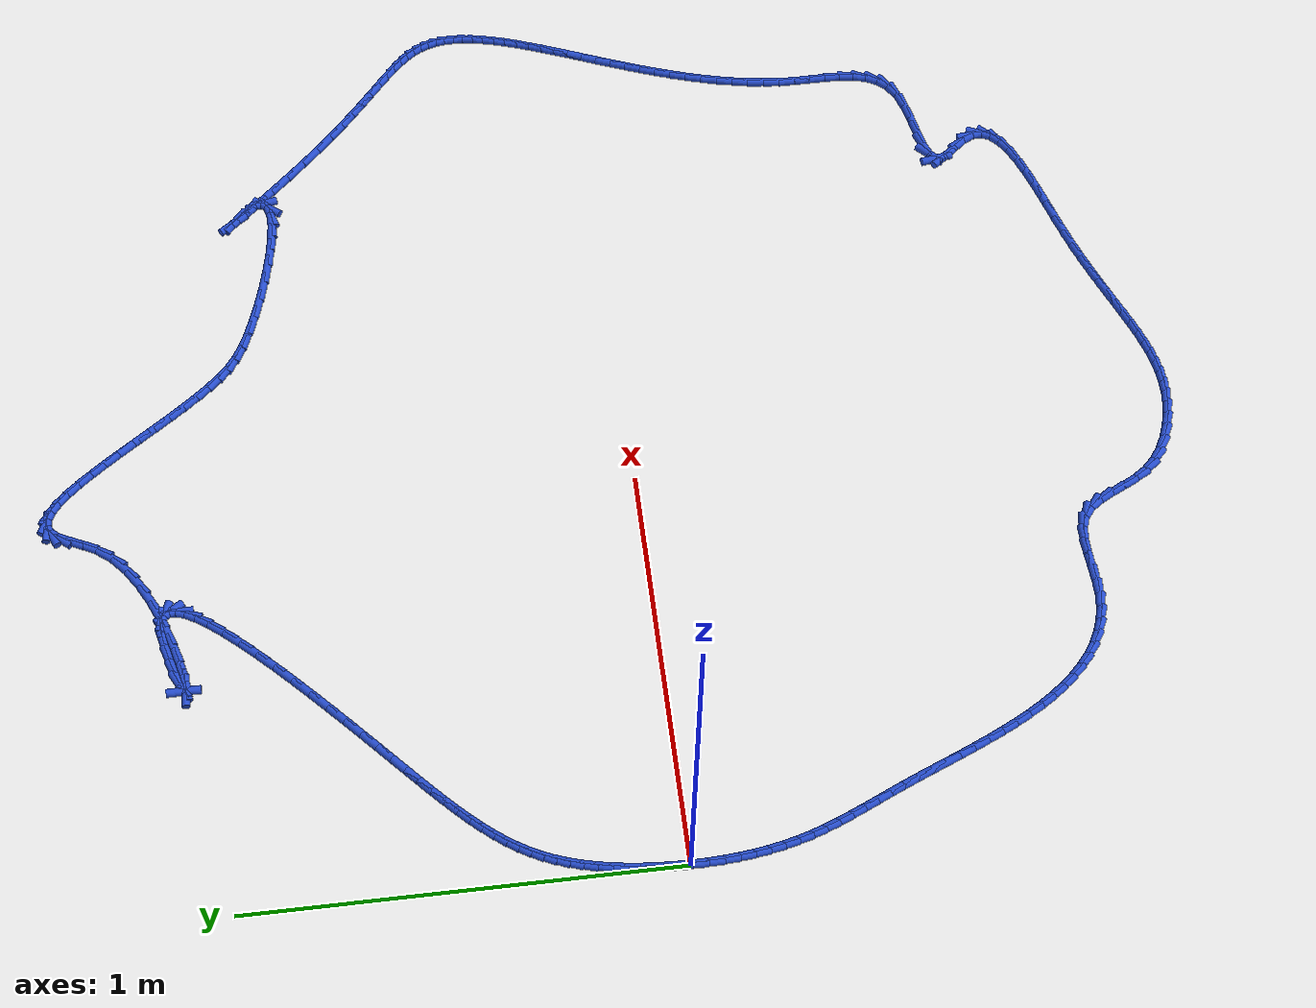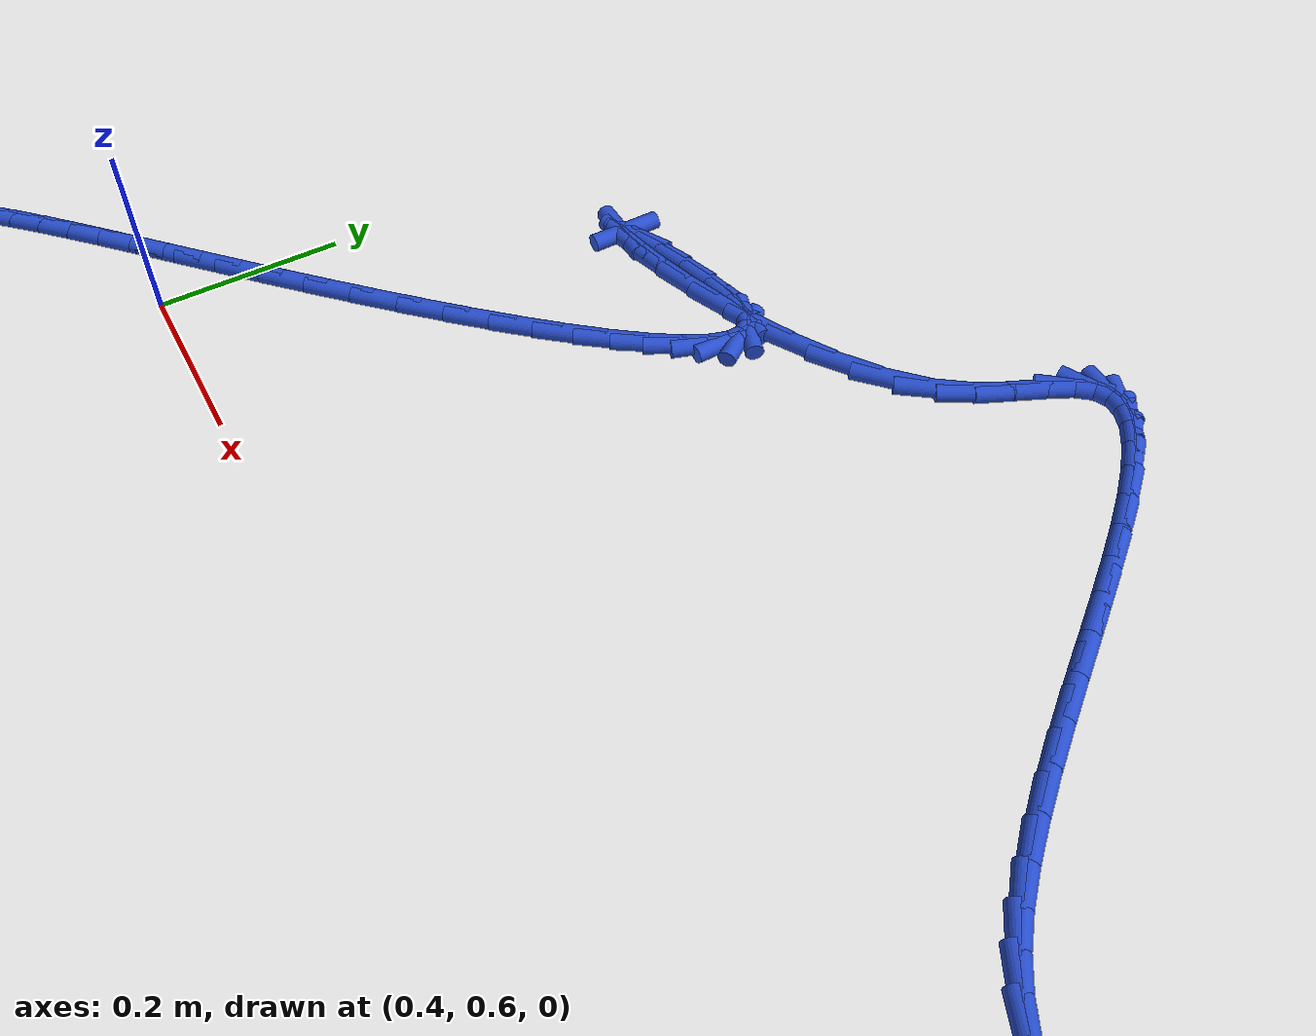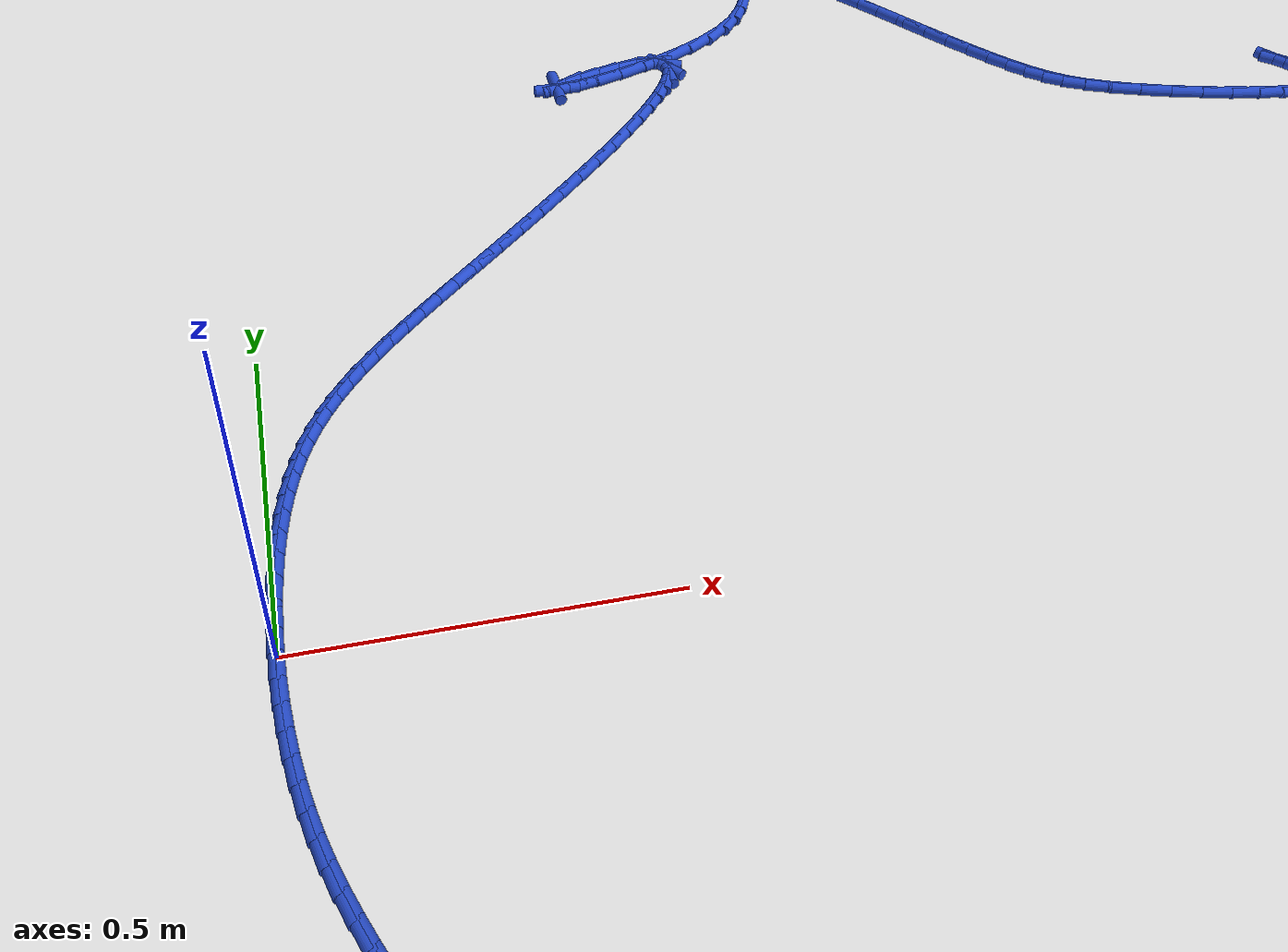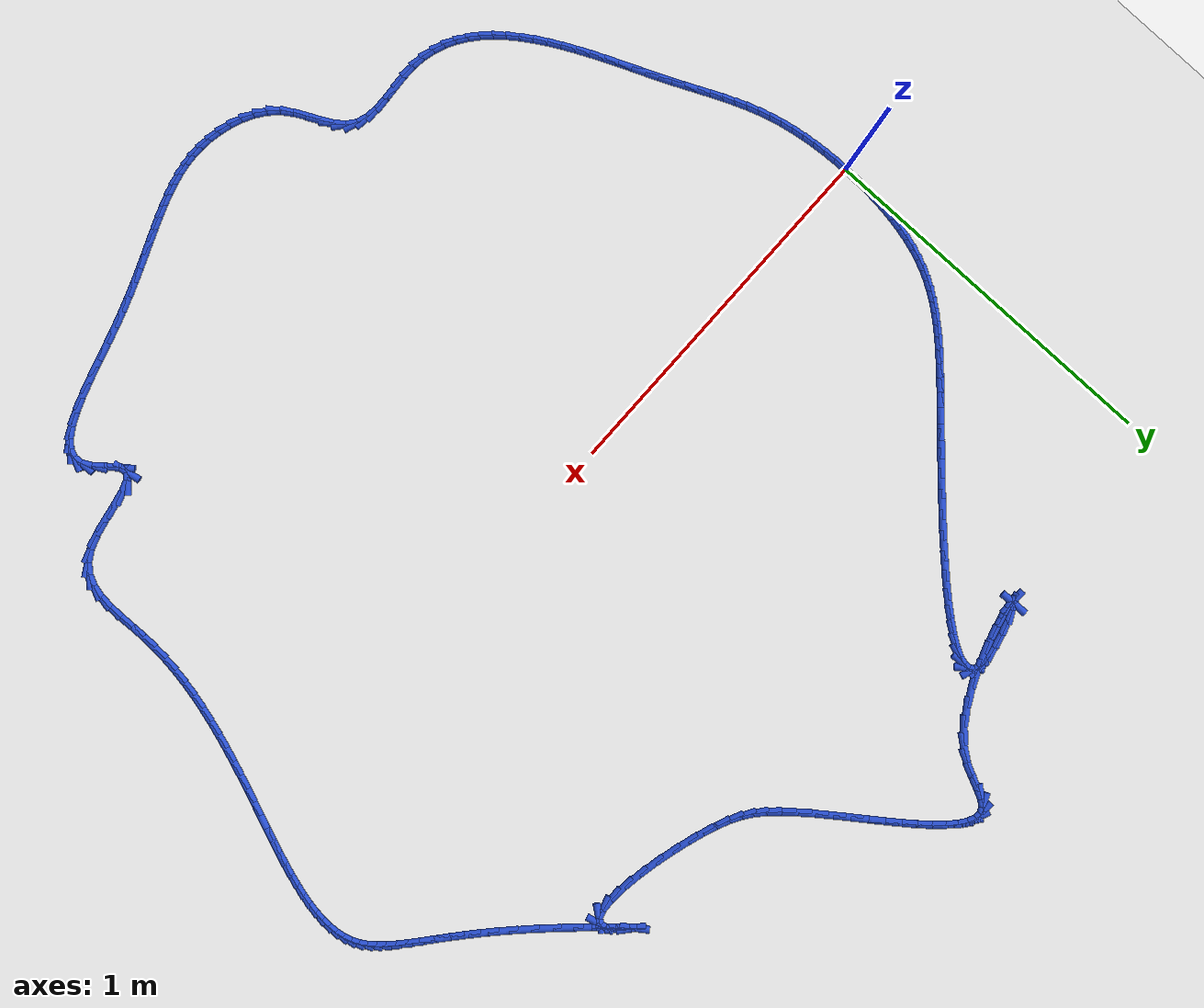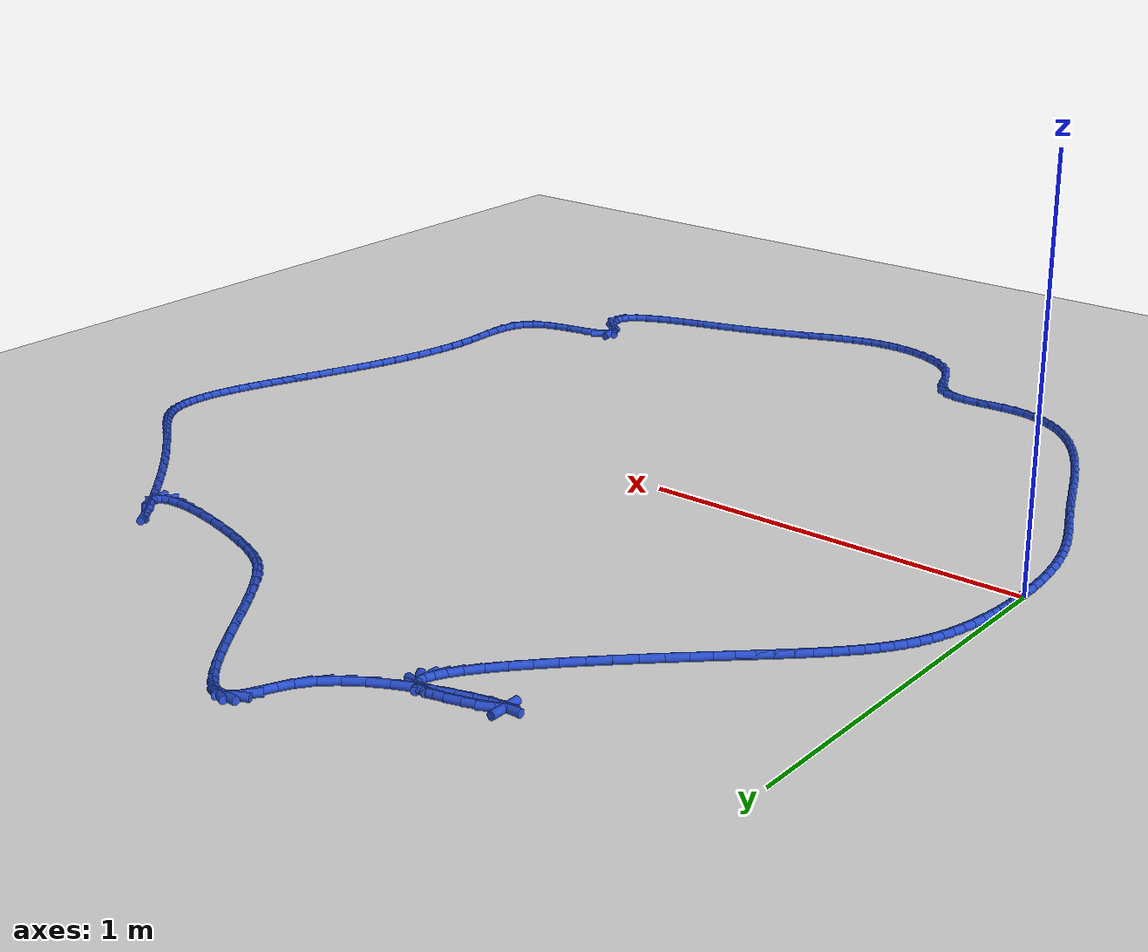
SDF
<sdf version="1.6">
 <world name="default">
  <light name="sun" type="directional">
   <pose>0 0 10 0 -0 0</pose>
   <diffuse>0.8 0.8 0.8 1</diffuse>
   <specular>0.2 0.2 0.2 1</specular>
   <attenuation>
    <range>1000</range>
    <constant>0.9</constant>
    <linear>0.01</linear>
    <quadratic>0.001</quadratic>
   </attenuation>
   <direction>-0.5 0.1 -0.9</direction>
  </light>
  <model name="ground_plane">
   <static>1</static>
   <link name="link">
    <collision name="collision">
     <geometry><plane><normal>0 0 1</normal><size>100 100</size></plane></geometry>
     <surface><friction><ode><mu>100</mu><mu2>50</mu2></ode></friction></surface>
    </collision>
    <visual name="visual">
     <cast_shadows>0</cast_shadows>
     <geometry><plane><normal>0 0 1</normal><size>100 100</size></plane></geometry>
     <material>
      <script><uri>file://media/materials/scripts/gazebo.material</uri><name>Gazebo/WhiteGlow</name></script>
     </material>
    </visual>
   </link>
  </model>
  <gravity>0 0 -9.8</gravity>
  <magnetic_field>6e-06 2.3e-05 -4.2e-05</magnetic_field>
  <atmosphere type="adiabatic"/>
  <physics name="default_physics" default="0" type="ode">
   <max_step_size>0.001</max_step_size>
   <real_time_factor>1</real_time_factor>
   <real_time_update_rate>1000</real_time_update_rate>
  </physics>
  <scene><ambient>0.4 0.4 0.4 1</ambient><background>0.7 0.7 0.7 1</background><shadows>1</shadows></scene>
  <spherical_coordinates>
   <surface_model>EARTH_WGS84</surface_model>
   <latitude_deg>0</latitude_deg>
   <longitude_deg>0</longitude_deg>
   <elevation>0</elevation>
   <heading_deg>0</heading_deg>
  </spherical_coordinates>
  <model name="line">
   <link name="link_0">
    <pose>-5.204170427930421e-18 1.3877787807814457e-17 0.01 0 1.57 1.5539956028132262</pose>
    <collision name="collision">
     <geometry><cylinder><radius>0.01</radius><length>0.08</length></cylinder></geometry>
    </collision>
    <visual name="visual">
     <material>
      <script><name>Gazebo/Blue</name><uri>file://media/materials/scripts/gazebo.material</uri></script>
     </material>
     <geometry><cylinder><radius>0.01</radius><length>0.08</length></cylinder></geometry>
    </visual>
   </link>
   <link name="link_1">
    <pose>0.0005980265331277306 0.03559193434376886 0.01 0 1.57 1.5232543392431086</pose>
    <collision name="collision">
     <geometry><cylinder><radius>0.01</radius><length>0.08</length></cylinder></geometry>
    </collision>
    <visual name="visual">
     <material>
      <script><name>Gazebo/Blue</name><uri>file://media/materials/scripts/gazebo.material</uri></script>
     </material>
     <geometry><cylinder><radius>0.01</radius><length>0.08</length></cylinder></geometry>
    </visual>
   </link>
   <link name="link_2">
    <pose>0.002291742754683563 0.07119078175580612 0.01 0 1.57 1.4909164867250893</pose>
    <collision name="collision">
     <geometry><cylinder><radius>0.01</radius><length>0.08</length></cylinder></geometry>
    </collision>
    <visual name="visual">
     <material>
      <script><name>Gazebo/Blue</name><uri>file://media/materials/scripts/gazebo.material</uri></script>
     </material>
     <geometry><cylinder><radius>0.01</radius><length>0.08</length></cylinder></geometry>
    </visual>
   </link>
   <link name="link_3">
    <pose>0.005120607771929287 0.10652943111934357 0.01 0 1.57 1.4562945144002444</pose>
    <collision name="collision">
     <geometry><cylinder><radius>0.01</radius><length>0.08</length></cylinder></geometry>
    </collision>
    <visual name="visual">
     <material>
      <script><name>Gazebo/Blue</name><uri>file://media/materials/scripts/gazebo.material</uri></script>
     </material>
     <geometry><cylinder><radius>0.01</radius><length>0.08</length></cylinder></geometry>
    </visual>
   </link>
   <link name="link_4">
    <pose>0.009124080692126687 0.14134077131761294 0.01 0 1.57 1.4186016950346203</pose>
    <collision name="collision">
     <geometry><cylinder><radius>0.01</radius><length>0.08</length></cylinder></geometry>
    </collision>
    <visual name="visual">
     <material>
      <script><name>Gazebo/Blue</name><uri>file://media/materials/scripts/gazebo.material</uri></script>
     </material>
     <geometry><cylinder><radius>0.01</radius><length>0.08</length></cylinder></geometry>
    </visual>
   </link>
   <link name="link_5">
    <pose>0.014341620622537552 0.1753576912338459 0.01 0 1.57 1.3769047832948358</pose>
    <collision name="collision">
     <geometry><cylinder><radius>0.01</radius><length>0.08</length></cylinder></geometry>
    </collision>
    <visual name="visual">
     <material>
      <script><name>Gazebo/Blue</name><uri>file://media/materials/scripts/gazebo.material</uri></script>
     </material>
     <geometry><cylinder><radius>0.01</radius><length>0.08</length></cylinder></geometry>
    </visual>
   </link>
   <link name="link_6">
    <pose>0.020812686670423686 0.20831307975127444 0.01 0 1.57 1.3300668114936554</pose>
    <collision name="collision">
     <geometry><cylinder><radius>0.01</radius><length>0.08</length></cylinder></geometry>
    </collision>
    <visual name="visual">
     <material>
      <script><name>Gazebo/Blue</name><uri>file://media/materials/scripts/gazebo.material</uri></script>
     </material>
     <geometry><cylinder><radius>0.01</radius><length>0.08</length></cylinder></geometry>
    </visual>
   </link>
   <link name="link_7">
    <pose>0.028576737943046847 0.23993982575312986 0.01 0 1.57 1.2767175931004857</pose>
    <collision name="collision">
     <geometry><cylinder><radius>0.01</radius><length>0.08</length></cylinder></geometry>
    </collision>
    <visual name="visual">
     <material>
      <script><name>Gazebo/Blue</name><uri>file://media/materials/scripts/gazebo.material</uri></script>
     </material>
     <geometry><cylinder><radius>0.01</radius><length>0.08</length></cylinder></geometry>
    </visual>
   </link>
   <link name="link_8">
    <pose>0.03767336790856834 0.2699755678706415 0.01 0 1.57 1.217369260622729</pose>
    <collision name="collision">
     <geometry><cylinder><radius>0.01</radius><length>0.08</length></cylinder></geometry>
    </collision>
    <visual name="visual">
     <material>
      <script><name>Gazebo/Blue</name><uri>file://media/materials/scripts/gazebo.material</uri></script>
     </material>
     <geometry><cylinder><radius>0.01</radius><length>0.08</length></cylinder></geometry>
    </visual>
   </link>
   <link name="link_9">
    <pose>0.04814813624060782 0.298368854103285 0.01 0 1.57 1.155319746181908</pose>
    <collision name="collision">
     <geometry><cylinder><radius>0.01</radius><length>0.08</length></cylinder></geometry>
    </collision>
    <visual name="visual">
     <material>
      <script><name>Gazebo/Blue</name><uri>file://media/materials/scripts/gazebo.material</uri></script>
     </material>
     <geometry><cylinder><radius>0.01</radius><length>0.08</length></cylinder></geometry>
    </visual>
   </link>
   <link name="link_10">
    <pose>0.06005481240099171 0.32535845397512186 0.01 0 1.57 1.092705463806939</pose>
    <collision name="collision">
     <geometry><cylinder><radius>0.01</radius><length>0.08</length></cylinder></geometry>
    </collision>
    <visual name="visual">
     <material>
      <script><name>Gazebo/Blue</name><uri>file://media/materials/scripts/gazebo.material</uri></script>
     </material>
     <geometry><cylinder><radius>0.01</radius><length>0.08</length></cylinder></geometry>
    </visual>
   </link>
   <link name="link_11">
    <pose>0.07344776331147915 0.35120425761992513 0.01 0 1.57 1.0316605319806469</pose>
    <collision name="collision">
     <geometry><cylinder><radius>0.01</radius><length>0.08</length></cylinder></geometry>
    </collision>
    <visual name="visual">
     <material>
      <script><name>Gazebo/Blue</name><uri>file://media/materials/scripts/gazebo.material</uri></script>
     </material>
     <geometry><cylinder><radius>0.01</radius><length>0.08</length></cylinder></geometry>
    </visual>
   </link>
   <link name="link_12">
    <pose>0.08838135589382916 0.37616615517146773 0.01 0 1.57 0.974214381793345</pose>
    <collision name="collision">
     <geometry><cylinder><radius>0.01</radius><length>0.08</length></cylinder></geometry>
    </collision>
    <visual name="visual">
     <material>
      <script><name>Gazebo/Blue</name><uri>file://media/materials/scripts/gazebo.material</uri></script>
     </material>
     <geometry><cylinder><radius>0.01</radius><length>0.08</length></cylinder></geometry>
    </visual>
   </link>
   <link name="link_13">
    <pose>0.10490995706980086 0.40050403676352275 0.01 0 1.57 0.9220393668527831</pose>
    <collision name="collision">
     <geometry><cylinder><radius>0.01</radius><length>0.08</length></cylinder></geometry>
    </collision>
    <visual name="visual">
     <material>
      <script><name>Gazebo/Blue</name><uri>file://media/materials/scripts/gazebo.material</uri></script>
     </material>
     <geometry><cylinder><radius>0.01</radius><length>0.08</length></cylinder></geometry>
    </visual>
   </link>
   <link name="link_14">
    <pose>0.12308793376115326 0.42447779252986295 0.01 0 1.57 0.8762941574746544</pose>
    <collision name="collision">
     <geometry><cylinder><radius>0.01</radius><length>0.08</length></cylinder></geometry>
    </collision>
    <visual name="visual">
     <material>
      <script><name>Gazebo/Blue</name><uri>file://media/materials/scripts/gazebo.material</uri></script>
     </material>
     <geometry><cylinder><radius>0.01</radius><length>0.08</length></cylinder></geometry>
    </visual>
   </link>
   <link name="link_15">
    <pose>0.14296965288964547 0.44834731260426147 0.01 0 1.57 0.8375864889348155</pose>
    <collision name="collision">
     <geometry><cylinder><radius>0.01</radius><length>0.08</length></cylinder></geometry>
    </collision>
    <visual name="visual">
     <material>
      <script><name>Gazebo/Blue</name><uri>file://media/materials/scripts/gazebo.material</uri></script>
     </material>
     <geometry><cylinder><radius>0.01</radius><length>0.08</length></cylinder></geometry>
    </visual>
   </link>
   <link name="link_16">
    <pose>0.1646094813770366 0.4723724871204913 0.01 0 1.57 0.8060331943420531</pose>
    <collision name="collision">
     <geometry><cylinder><radius>0.01</radius><length>0.08</length></cylinder></geometry>
    </collision>
    <visual name="visual">
     <material>
      <script><name>Gazebo/Blue</name><uri>file://media/materials/scripts/gazebo.material</uri></script>
     </material>
     <geometry><cylinder><radius>0.01</radius><length>0.08</length></cylinder></geometry>
    </visual>
   </link>
   <link name="link_17">
    <pose>0.18806178614508567 0.49681320621232533 0.01 0 1.57 0.781373342170855</pose>
    <collision name="collision">
     <geometry><cylinder><radius>0.01</radius><length>0.08</length></cylinder></geometry>
    </collision>
    <visual name="visual">
     <material>
      <script><name>Gazebo/Blue</name><uri>file://media/materials/scripts/gazebo.material</uri></script>
     </material>
     <geometry><cylinder><radius>0.01</radius><length>0.08</length></cylinder></geometry>
    </visual>
   </link>
   <link name="link_18">
    <pose>0.21338093411555187 0.5219293600135366 0.01 0 1.57 0.763093015876436</pose>
    <collision name="collision">
     <geometry><cylinder><radius>0.01</radius><length>0.08</length></cylinder></geometry>
    </collision>
    <visual name="visual">
     <material>
      <script><name>Gazebo/Blue</name><uri>file://media/materials/scripts/gazebo.material</uri></script>
     </material>
     <geometry><cylinder><radius>0.01</radius><length>0.08</length></cylinder></geometry>
    </visual>
   </link>
   <link name="link_19">
    <pose>0.24062129221019404 0.5479808386578979 0.01 0 1.57 0.7505353933836121</pose>
    <collision name="collision">
     <geometry><cylinder><radius>0.01</radius><length>0.08</length></cylinder></geometry>
    </collision>
    <visual name="visual">
     <material>
      <script><name>Gazebo/Blue</name><uri>file://media/materials/scripts/gazebo.material</uri></script>
     </material>
     <geometry><cylinder><radius>0.01</radius><length>0.08</length></cylinder></geometry>
    </visual>
   </link>
   <link name="link_20">
    <pose>0.26983722735077154 0.5752275322791827 0.01 0 1.57 0.7429852658735079</pose>
    <collision name="collision">
     <geometry><cylinder><radius>0.01</radius><length>0.08</length></cylinder></geometry>
    </collision>
    <visual name="visual">
     <material>
      <script><name>Gazebo/Blue</name><uri>file://media/materials/scripts/gazebo.material</uri></script>
     </material>
     <geometry><cylinder><radius>0.01</radius><length>0.08</length></cylinder></geometry>
    </visual>
   </link>
   <link name="link_21">
    <pose>0.3010831064590433 0.6039293310111634 0.01 0 1.57 0.7397274515082792</pose>
    <collision name="collision">
     <geometry><cylinder><radius>0.01</radius><length>0.08</length></cylinder></geometry>
    </collision>
    <visual name="visual">
     <material>
      <script><name>Gazebo/Blue</name><uri>file://media/materials/scripts/gazebo.material</uri></script>
     </material>
     <geometry><cylinder><radius>0.01</radius><length>0.08</length></cylinder></geometry>
    </visual>
   </link>
   <link name="link_22">
    <pose>0.33441329645676837 0.6343461249876132 0.01 0 1.57 0.7400832182587512</pose>
    <collision name="collision">
     <geometry><cylinder><radius>0.01</radius><length>0.08</length></cylinder></geometry>
    </collision>
    <visual name="visual">
     <material>
      <script><name>Gazebo/Blue</name><uri>file://media/materials/scripts/gazebo.material</uri></script>
     </material>
     <geometry><cylinder><radius>0.01</radius><length>0.08</length></cylinder></geometry>
    </visual>
   </link>
   <link name="link_23">
    <pose>0.36988198044958814 0.666737622033864 0.01 0 1.57 0.7432469256478808</pose>
    <collision name="collision">
     <geometry><cylinder><radius>0.01</radius><length>0.08</length></cylinder></geometry>
    </collision>
    <visual name="visual">
     <material>
      <script><name>Gazebo/Blue</name><uri>file://media/materials/scripts/gazebo.material</uri></script>
     </material>
     <geometry><cylinder><radius>0.01</radius><length>0.08</length></cylinder></geometry>
    </visual>
   </link>
   <link name="link_24">
    <pose>0.40736722309887724 0.7011888560704462 0.01 0 1.57 0.7483380536034715</pose>
    <collision name="collision">
     <geometry><cylinder><radius>0.01</radius><length>0.08</length></cylinder></geometry>
    </collision>
    <visual name="visual">
     <material>
      <script><name>Gazebo/Blue</name><uri>file://media/materials/scripts/gazebo.material</uri></script>
     </material>
     <geometry><cylinder><radius>0.01</radius><length>0.08</length></cylinder></geometry>
    </visual>
   </link>
   <link name="link_25">
    <pose>0.44624284087430577 0.7372847487156237 0.01 0 1.57 0.7552770348175272</pose>
    <collision name="collision">
     <geometry><cylinder><radius>0.01</radius><length>0.08</length></cylinder></geometry>
    </collision>
    <visual name="visual">
     <material>
      <script><name>Gazebo/Blue</name><uri>file://media/materials/scripts/gazebo.material</uri></script>
     </material>
     <geometry><cylinder><radius>0.01</radius><length>0.08</length></cylinder></geometry>
    </visual>
   </link>
   <link name="link_26">
    <pose>0.4857929780434317 0.7745212848850892 0.01 0 1.57 0.7642641344676553</pose>
    <collision name="collision">
     <geometry><cylinder><radius>0.01</radius><length>0.08</length></cylinder></geometry>
    </collision>
    <visual name="visual">
     <material>
      <script><name>Gazebo/Blue</name><uri>file://media/materials/scripts/gazebo.material</uri></script>
     </material>
     <geometry><cylinder><radius>0.01</radius><length>0.08</length></cylinder></geometry>
    </visual>
   </link>
   <link name="link_27">
    <pose>0.5253017788738142 0.8123944494945362 0.01 0 1.57 0.775681739288513</pose>
    <collision name="collision">
     <geometry><cylinder><radius>0.01</radius><length>0.08</length></cylinder></geometry>
    </collision>
    <visual name="visual">
     <material>
      <script><name>Gazebo/Blue</name><uri>file://media/materials/scripts/gazebo.material</uri></script>
     </material>
     <geometry><cylinder><radius>0.01</radius><length>0.08</length></cylinder></geometry>
    </visual>
   </link>
   <link name="link_28">
    <pose>0.5640533876330114 0.8504002274596576 0.01 0 1.57 0.7901478450757111</pose>
    <collision name="collision">
     <geometry><cylinder><radius>0.01</radius><length>0.08</length></cylinder></geometry>
    </collision>
    <visual name="visual">
     <material>
      <script><name>Gazebo/Blue</name><uri>file://media/materials/scripts/gazebo.material</uri></script>
     </material>
     <geometry><cylinder><radius>0.01</radius><length>0.08</length></cylinder></geometry>
    </visual>
   </link>
   <link name="link_29">
    <pose>0.6013319485885817 0.8880346036961467 0.01 0 1.57 0.8086275839689925</pose>
    <collision name="collision">
     <geometry><cylinder><radius>0.01</radius><length>0.08</length></cylinder></geometry>
    </collision>
    <visual name="visual">
     <material>
      <script><name>Gazebo/Blue</name><uri>file://media/materials/scripts/gazebo.material</uri></script>
     </material>
     <geometry><cylinder><radius>0.01</radius><length>0.08</length></cylinder></geometry>
    </visual>
   </link>
   <link name="link_30">
    <pose>0.6364216060080834 0.9247935631196958 0.01 0 1.57 0.8326456880423339</pose>
    <collision name="collision">
     <geometry><cylinder><radius>0.01</radius><length>0.08</length></cylinder></geometry>
    </collision>
    <visual name="visual">
     <material>
      <script><name>Gazebo/Blue</name><uri>file://media/materials/scripts/gazebo.material</uri></script>
     </material>
     <geometry><cylinder><radius>0.01</radius><length>0.08</length></cylinder></geometry>
    </visual>
   </link>
   <link name="link_31">
    <pose>0.6686065041590754 0.960173090645999 0.01 0 1.57 0.8646992603622173</pose>
    <collision name="collision">
     <geometry><cylinder><radius>0.01</radius><length>0.08</length></cylinder></geometry>
    </collision>
    <visual name="visual">
     <material>
      <script><name>Gazebo/Blue</name><uri>file://media/materials/scripts/gazebo.material</uri></script>
     </material>
     <geometry><cylinder><radius>0.01</radius><length>0.08</length></cylinder></geometry>
    </visual>
   </link>
   <link name="link_32">
    <pose>0.6971707873091159 0.993669171190749 0.01 0 1.57 0.9091081395844214</pose>
    <collision name="collision">
     <geometry><cylinder><radius>0.01</radius><length>0.08</length></cylinder></geometry>
    </collision>
    <visual name="visual">
     <material>
      <script><name>Gazebo/Blue</name><uri>file://media/materials/scripts/gazebo.material</uri></script>
     </material>
     <geometry><cylinder><radius>0.01</radius><length>0.08</length></cylinder></geometry>
    </visual>
   </link>
   <link name="link_33">
    <pose>0.7213985997257629 1.0247777896696384 0.01 0 1.57 0.9739146564178902</pose>
    <collision name="collision">
     <geometry><cylinder><radius>0.01</radius><length>0.08</length></cylinder></geometry>
    </collision>
    <visual name="visual">
     <material>
      <script><name>Gazebo/Blue</name><uri>file://media/materials/scripts/gazebo.material</uri></script>
     </material>
     <geometry><cylinder><radius>0.01</radius><length>0.08</length></cylinder></geometry>
    </visual>
   </link>
   <link name="link_34">
    <pose>0.7405740856765752 1.0529949309983604 0.01 0 1.57 1.0755503664429282</pose>
    <collision name="collision">
     <geometry><cylinder><radius>0.01</radius><length>0.08</length></cylinder></geometry>
    </collision>
    <visual name="visual">
     <material>
      <script><name>Gazebo/Blue</name><uri>file://media/materials/scripts/gazebo.material</uri></script>
     </material>
     <geometry><cylinder><radius>0.01</radius><length>0.08</length></cylinder></geometry>
    </visual>
   </link>
   <link name="link_35">
    <pose>0.7539813894291112 1.0778165800926083 0.01 0 1.57 1.25123180687238</pose>
    <collision name="collision">
     <geometry><cylinder><radius>0.01</radius><length>0.08</length></cylinder></geometry>
    </collision>
    <visual name="visual">
     <material>
      <script><name>Gazebo/Blue</name><uri>file://media/materials/scripts/gazebo.material</uri></script>
     </material>
     <geometry><cylinder><radius>0.01</radius><length>0.08</length></cylinder></geometry>
    </visual>
   </link>
   <link name="link_36">
    <pose>0.7609046552509291 1.0987387218680749 0.01 0 1.57 -1.5540514657367226</pose>
    <collision name="collision">
     <geometry><cylinder><radius>0.01</radius><length>0.08</length></cylinder></geometry>
    </collision>
    <visual name="visual">
     <material>
      <script><name>Gazebo/Blue</name><uri>file://media/materials/scripts/gazebo.material</uri></script>
     </material>
     <geometry><cylinder><radius>0.01</radius><length>0.08</length></cylinder></geometry>
    </visual>
   </link>
   <link name="link_37">
    <pose>0.760628027409588 1.1152573412404536 0.01 0 1.57 -0.9563449752880794</pose>
    <collision name="collision">
     <geometry><cylinder><radius>0.01</radius><length>0.08</length></cylinder></geometry>
    </collision>
    <visual name="visual">
     <material>
      <script><name>Gazebo/Blue</name><uri>file://media/materials/scripts/gazebo.material</uri></script>
     </material>
     <geometry><cylinder><radius>0.01</radius><length>0.08</length></cylinder></geometry>
    </visual>
   </link>
   <link name="link_38">
    <pose>0.7524356501726457 1.1268684231254376 0.01 0 1.57 -0.3530542364595933</pose>
    <collision name="collision">
     <geometry><cylinder><radius>0.01</radius><length>0.08</length></cylinder></geometry>
    </collision>
    <visual name="visual">
     <material>
      <script><name>Gazebo/Blue</name><uri>file://media/materials/scripts/gazebo.material</uri></script>
     </material>
     <geometry><cylinder><radius>0.01</radius><length>0.08</length></cylinder></geometry>
    </visual>
   </link>
   <link name="link_39">
    <pose>0.7356116678076605 1.1330679524387193 0.01 0 1.57 -0.010854746388954558</pose>
    <collision name="collision">
     <geometry><cylinder><radius>0.01</radius><length>0.08</length></cylinder></geometry>
    </collision>
    <visual name="visual">
     <material>
      <script><name>Gazebo/Blue</name><uri>file://media/materials/scripts/gazebo.material</uri></script>
     </material>
     <geometry><cylinder><radius>0.01</radius><length>0.08</length></cylinder></geometry>
    </visual>
   </link>
   <link name="link_40">
    <pose>0.7094405324332714 1.133352044633777 0.01 0 1.57 0.1583651510524637</pose>
    <collision name="collision">
     <geometry><cylinder><radius>0.01</radius><length>0.08</length></cylinder></geometry>
    </collision>
    <visual name="visual">
     <material>
      <script><name>Gazebo/Blue</name><uri>file://media/materials/scripts/gazebo.material</uri></script>
     </material>
     <geometry><cylinder><radius>0.01</radius><length>0.08</length></cylinder></geometry>
    </visual>
   </link>
   <link name="link_41">
    <pose>0.6745255048374678 1.1277760282832954 0.01 0 1.57 0.2416256211021858</pose>
    <collision name="collision">
     <geometry><cylinder><radius>0.01</radius><length>0.08</length></cylinder></geometry>
    </collision>
    <visual name="visual">
     <material>
      <script><name>Gazebo/Blue</name><uri>file://media/materials/scripts/gazebo.material</uri></script>
     </material>
     <geometry><cylinder><radius>0.01</radius><length>0.08</length></cylinder></geometry>
    </visual>
   </link>
   <link name="link_42">
    <pose>0.6358065200842399 1.118234107609792 0.01 0 1.57 0.29715572822820807</pose>
    <collision name="collision">
     <geometry><cylinder><radius>0.01</radius><length>0.08</length></cylinder></geometry>
    </collision>
    <visual name="visual">
     <material>
      <script><name>Gazebo/Blue</name><uri>file://media/materials/scripts/gazebo.material</uri></script>
     </material>
     <geometry><cylinder><radius>0.01</radius><length>0.08</length></cylinder></geometry>
    </visual>
   </link>
   <link name="link_43">
    <pose>0.5991135902482395 1.106997905299156 0.01 0 1.57 0.35405112781368203</pose>
    <collision name="collision">
     <geometry><cylinder><radius>0.01</radius><length>0.08</length></cylinder></geometry>
    </collision>
    <visual name="visual">
     <material>
      <script><name>Gazebo/Blue</name><uri>file://media/materials/scripts/gazebo.material</uri></script>
     </material>
     <geometry><cylinder><radius>0.01</radius><length>0.08</length></cylinder></geometry>
    </visual>
   </link>
   <link name="link_44">
    <pose>0.5702767274041195 1.096339044037277 0.01 0 1.57 0.47408787551091924</pose>
    <collision name="collision">
     <geometry><cylinder><radius>0.01</radius><length>0.08</length></cylinder></geometry>
    </collision>
    <visual name="visual">
     <material>
      <script><name>Gazebo/Blue</name><uri>file://media/materials/scripts/gazebo.material</uri></script>
     </material>
     <geometry><cylinder><radius>0.01</radius><length>0.08</length></cylinder></geometry>
    </visual>
   </link>
   <link name="link_45">
    <pose>0.5549633225509331 1.0884814405461478 0.01 0 1.57 -1.558439855262049</pose>
    <collision name="collision">
     <geometry><cylinder><radius>0.01</radius><length>0.08</length></cylinder></geometry>
    </collision>
    <visual name="visual">
     <material>
      <script><name>Gazebo/Blue</name><uri>file://media/materials/scripts/gazebo.material</uri></script>
     </material>
     <geometry><cylinder><radius>0.01</radius><length>0.08</length></cylinder></geometry>
    </visual>
   </link>
   <link name="link_46">
    <pose>0.5550122018490914 1.0845258768292934 0.01 0 1.57 -0.006764573152920737</pose>
    <collision name="collision">
     <geometry><cylinder><radius>0.01</radius><length>0.08</length></cylinder></geometry>
    </collision>
    <visual name="visual">
     <material>
      <script><name>Gazebo/Blue</name><uri>file://media/materials/scripts/gazebo.material</uri></script>
     </material>
     <geometry><cylinder><radius>0.01</radius><length>0.08</length></cylinder></geometry>
    </visual>
   </link>
   <link name="link_47">
    <pose>0.5683839302516518 1.084435421414599 0.01 0 1.57 0.1494776019934119</pose>
    <collision name="collision">
     <geometry><cylinder><radius>0.01</radius><length>0.08</length></cylinder></geometry>
    </collision>
    <visual name="visual">
     <material>
      <script><name>Gazebo/Blue</name><uri>file://media/materials/scripts/gazebo.material</uri></script>
     </material>
     <geometry><cylinder><radius>0.01</radius><length>0.08</length></cylinder></geometry>
    </visual>
   </link>
   <link name="link_48">
    <pose>0.592866511844081 1.0881225209625913 0.01 0 1.57 0.21749831749132445</pose>
    <collision name="collision">
     <geometry><cylinder><radius>0.01</radius><length>0.08</length></cylinder></geometry>
    </collision>
    <visual name="visual">
     <material>
      <script><name>Gazebo/Blue</name><uri>file://media/materials/scripts/gazebo.material</uri></script>
     </material>
     <geometry><cylinder><radius>0.01</radius><length>0.08</length></cylinder></geometry>
    </visual>
   </link>
   <link name="link_49">
    <pose>0.6262479507118455 1.095499622133796 0.01 0 1.57 0.2674556698785728</pose>
    <collision name="collision">
     <geometry><cylinder><radius>0.01</radius><length>0.08</length></cylinder></geometry>
    </collision>
    <visual name="visual">
     <material>
      <script><name>Gazebo/Blue</name><uri>file://media/materials/scripts/gazebo.material</uri></script>
     </material>
     <geometry><cylinder><radius>0.01</radius><length>0.08</length></cylinder></geometry>
    </visual>
   </link>
   <link name="link_50">
    <pose>0.6663162509404124 1.1064791715887397 0.01 0 1.57 0.31459563817116315</pose>
    <collision name="collision">
     <geometry><cylinder><radius>0.01</radius><length>0.08</length></cylinder></geometry>
    </collision>
    <visual name="visual">
     <material>
      <script><name>Gazebo/Blue</name><uri>file://media/materials/scripts/gazebo.material</uri></script>
     </material>
     <geometry><cylinder><radius>0.01</radius><length>0.08</length></cylinder></geometry>
    </visual>
   </link>
   <link name="link_51">
    <pose>0.7108594166152474 1.1209736159879482 0.01 0 1.57 0.3656740829068888</pose>
    <collision name="collision">
     <geometry><cylinder><radius>0.01</radius><length>0.08</length></cylinder></geometry>
    </collision>
    <visual name="visual">
     <material>
      <script><name>Gazebo/Blue</name><uri>file://media/materials/scripts/gazebo.material</uri></script>
     </material>
     <geometry><cylinder><radius>0.01</radius><length>0.08</length></cylinder></geometry>
    </visual>
   </link>
   <link name="link_52">
    <pose>0.7576654518218182 1.138895401991948 0.01 0 1.57 0.425972506936103</pose>
    <collision name="collision">
     <geometry><cylinder><radius>0.01</radius><length>0.08</length></cylinder></geometry>
    </collision>
    <visual name="visual">
     <material>
      <script><name>Gazebo/Blue</name><uri>file://media/materials/scripts/gazebo.material</uri></script>
     </material>
     <geometry><cylinder><radius>0.01</radius><length>0.08</length></cylinder></geometry>
    </visual>
   </link>
   <link name="link_53">
    <pose>0.8045223606455906 1.1601569762612647 0.01 0 1.57 0.5016593800901276</pose>
    <collision name="collision">
     <geometry><cylinder><radius>0.01</radius><length>0.08</length></cylinder></geometry>
    </collision>
    <visual name="visual">
     <material>
      <script><name>Gazebo/Blue</name><uri>file://media/materials/scripts/gazebo.material</uri></script>
     </material>
     <geometry><cylinder><radius>0.01</radius><length>0.08</length></cylinder></geometry>
    </visual>
   </link>
   <link name="link_54">
    <pose>0.8492181471720317 1.1846707854564247 0.01 0 1.57 0.6015570599321184</pose>
    <collision name="collision">
     <geometry><cylinder><radius>0.01</radius><length>0.08</length></cylinder></geometry>
    </collision>
    <visual name="visual">
     <material>
      <script><name>Gazebo/Blue</name><uri>file://media/materials/scripts/gazebo.material</uri></script>
     </material>
     <geometry><cylinder><radius>0.01</radius><length>0.08</length></cylinder></geometry>
    </visual>
   </link>
   <link name="link_55">
    <pose>0.8895408154866081 1.2123492762379544 0.01 0 1.57 0.7391946228261188</pose>
    <collision name="collision">
     <geometry><cylinder><radius>0.01</radius><length>0.08</length></cylinder></geometry>
    </collision>
    <visual name="visual">
     <material>
      <script><name>Gazebo/Blue</name><uri>file://media/materials/scripts/gazebo.material</uri></script>
     </material>
     <geometry><cylinder><radius>0.01</radius><length>0.08</length></cylinder></geometry>
    </visual>
   </link>
   <link name="link_56">
    <pose>0.9232783696747864 1.2431048952663795 0.01 0 1.57 0.920132694141095</pose>
    <collision name="collision">
     <geometry><cylinder><radius>0.01</radius><length>0.08</length></cylinder></geometry>
    </collision>
    <visual name="visual">
     <material>
      <script><name>Gazebo/Blue</name><uri>file://media/materials/scripts/gazebo.material</uri></script>
     </material>
     <geometry><cylinder><radius>0.01</radius><length>0.08</length></cylinder></geometry>
    </visual>
   </link>
   <link name="link_57">
    <pose>0.9487313663142984 1.2765405958409337 0.01 0 1.57 1.0674545138072022</pose>
    <collision name="collision">
     <geometry><cylinder><radius>0.01</radius><length>0.08</length></cylinder></geometry>
    </collision>
    <visual name="visual">
     <material>
      <script><name>Gazebo/Blue</name><uri>file://media/materials/scripts/gazebo.material</uri></script>
     </material>
     <geometry><cylinder><radius>0.01</radius><length>0.08</length></cylinder></geometry>
    </visual>
   </link>
   <link name="link_58">
    <pose>0.9673519717356975 1.310356302184608 0.01 0 1.57 1.137068824267305</pose>
    <collision name="collision">
     <geometry><cylinder><radius>0.01</radius><length>0.08</length></cylinder></geometry>
    </collision>
    <visual name="visual">
     <material>
      <script><name>Gazebo/Blue</name><uri>file://media/materials/scripts/gazebo.material</uri></script>
     </material>
     <geometry><cylinder><radius>0.01</radius><length>0.08</length></cylinder></geometry>
    </visual>
   </link>
   <link name="link_59">
    <pose>0.9817893713539211 1.3415291453127736 0.01 0 1.57 1.1023667718908936</pose>
    <collision name="collision">
     <geometry><cylinder><radius>0.01</radius><length>0.08</length></cylinder></geometry>
    </collision>
    <visual name="visual">
     <material>
      <script><name>Gazebo/Blue</name><uri>file://media/materials/scripts/gazebo.material</uri></script>
     </material>
     <geometry><cylinder><radius>0.01</radius><length>0.08</length></cylinder></geometry>
    </visual>
   </link>
   <link name="link_60">
    <pose>0.9946950560434099 1.3670348641406338 0.01 0 1.57 0.8813371569077888</pose>
    <collision name="collision">
     <geometry><cylinder><radius>0.01</radius><length>0.08</length></cylinder></geometry>
    </collision>
    <visual name="visual">
     <material>
      <script><name>Gazebo/Blue</name><uri>file://media/materials/scripts/gazebo.material</uri></script>
     </material>
     <geometry><cylinder><radius>0.01</radius><length>0.08</length></cylinder></geometry>
    </visual>
   </link>
   <link name="link_61">
    <pose>1.0086441090595615 1.3839545529769235 0.01 0 1.57 0.43048380451970086</pose>
    <collision name="collision">
     <geometry><cylinder><radius>0.01</radius><length>0.08</length></cylinder></geometry>
    </collision>
    <visual name="visual">
     <material>
      <script><name>Gazebo/Blue</name><uri>file://media/materials/scripts/gazebo.material</uri></script>
     </material>
     <geometry><cylinder><radius>0.01</radius><length>0.08</length></cylinder></geometry>
    </visual>
   </link>
   <link name="link_62">
    <pose>1.0247685956993833 1.3913590255691382 0.01 0 1.57 -0.0695958296253201</pose>
    <collision name="collision">
     <geometry><cylinder><radius>0.01</radius><length>0.08</length></cylinder></geometry>
    </collision>
    <visual name="visual">
     <material>
      <script><name>Gazebo/Blue</name><uri>file://media/materials/scripts/gazebo.material</uri></script>
     </material>
     <geometry><cylinder><radius>0.01</radius><length>0.08</length></cylinder></geometry>
    </visual>
   </link>
   <link name="link_63">
    <pose>1.0429132152024498 1.390094192956103 0.01 0 1.57 -0.4246035085404892</pose>
    <collision name="collision">
     <geometry><cylinder><radius>0.01</radius><length>0.08</length></cylinder></geometry>
    </collision>
    <visual name="visual">
     <material>
      <script><name>Gazebo/Blue</name><uri>file://media/materials/scripts/gazebo.material</uri></script>
     </material>
     <geometry><cylinder><radius>0.01</radius><length>0.08</length></cylinder></geometry>
    </visual>
   </link>
   <link name="link_64">
    <pose>1.0628775167572475 1.3810682217665922 0.01 0 1.57 -0.6342842541538061</pose>
    <collision name="collision">
     <geometry><cylinder><radius>0.01</radius><length>0.08</length></cylinder></geometry>
    </collision>
    <visual name="visual">
     <material>
      <script><name>Gazebo/Blue</name><uri>file://media/materials/scripts/gazebo.material</uri></script>
     </material>
     <geometry><cylinder><radius>0.01</radius><length>0.08</length></cylinder></geometry>
    </visual>
   </link>
   <link name="link_65">
    <pose>1.0844610495522642 1.3651892786293804 0.01 0 1.57 -0.7591122647836013</pose>
    <collision name="collision">
     <geometry><cylinder><radius>0.01</radius><length>0.08</length></cylinder></geometry>
    </collision>
    <visual name="visual">
     <material>
      <script><name>Gazebo/Blue</name><uri>file://media/materials/scripts/gazebo.material</uri></script>
     </material>
     <geometry><cylinder><radius>0.01</radius><length>0.08</length></cylinder></geometry>
    </visual>
   </link>
   <link name="link_66">
    <pose>1.1074633627759871 1.3433655301732428 0.01 0 1.57 -0.8370298197613192</pose>
    <collision name="collision">
     <geometry><cylinder><radius>0.01</radius><length>0.08</length></cylinder></geometry>
    </collision>
    <visual name="visual">
     <material>
      <script><name>Gazebo/Blue</name><uri>file://media/materials/scripts/gazebo.material</uri></script>
     </material>
     <geometry><cylinder><radius>0.01</radius><length>0.08</length></cylinder></geometry>
    </visual>
   </link>
   <link name="link_67">
    <pose>1.1316840056169029 1.3165051430269532 0.01 0 1.57 -0.8873131862566405</pose>
    <collision name="collision">
     <geometry><cylinder><radius>0.01</radius><length>0.08</length></cylinder></geometry>
    </collision>
    <visual name="visual">
     <material>
      <script><name>Gazebo/Blue</name><uri>file://media/materials/scripts/gazebo.material</uri></script>
     </material>
     <geometry><cylinder><radius>0.01</radius><length>0.08</length></cylinder></geometry>
    </visual>
   </link>
   <link name="link_68">
    <pose>1.1569225272634998 1.2855162838192866 0.01 0 1.57 -0.9198708373193974</pose>
    <collision name="collision">
     <geometry><cylinder><radius>0.01</radius><length>0.08</length></cylinder></geometry>
    </collision>
    <visual name="visual">
     <material>
      <script><name>Gazebo/Blue</name><uri>file://media/materials/scripts/gazebo.material</uri></script>
     </material>
     <geometry><cylinder><radius>0.01</radius><length>0.08</length></cylinder></geometry>
    </visual>
   </link>
   <link name="link_69">
    <pose>1.1829784769042644 1.2513071191790184 0.01 0 1.57 -0.9399975524762053</pose>
    <collision name="collision">
     <geometry><cylinder><radius>0.01</radius><length>0.08</length></cylinder></geometry>
    </collision>
    <visual name="visual">
     <material>
      <script><name>Gazebo/Blue</name><uri>file://media/materials/scripts/gazebo.material</uri></script>
     </material>
     <geometry><cylinder><radius>0.01</radius><length>0.08</length></cylinder></geometry>
    </visual>
   </link>
   <link name="link_70">
    <pose>1.2096514037276849 1.2147858157349216 0.01 0 1.57 -0.9505473539609733</pose>
    <collision name="collision">
     <geometry><cylinder><radius>0.01</radius><length>0.08</length></cylinder></geometry>
    </collision>
    <visual name="visual">
     <material>
      <script><name>Gazebo/Blue</name><uri>file://media/materials/scripts/gazebo.material</uri></script>
     </material>
     <geometry><cylinder><radius>0.01</radius><length>0.08</length></cylinder></geometry>
    </visual>
   </link>
   <link name="link_71">
    <pose>1.2367408569222473 1.1768605401157723 0.01 0 1.57 -0.9529309636579488</pose>
    <collision name="collision">
     <geometry><cylinder><radius>0.01</radius><length>0.08</length></cylinder></geometry>
    </collision>
    <visual name="visual">
     <material>
      <script><name>Gazebo/Blue</name><uri>file://media/materials/scripts/gazebo.material</uri></script>
     </material>
     <geometry><cylinder><radius>0.01</radius><length>0.08</length></cylinder></geometry>
    </visual>
   </link>
   <link name="link_72">
    <pose>1.2640463856764397 1.1384394589503446 0.01 0 1.57 -0.947555607154451</pose>
    <collision name="collision">
     <geometry><cylinder><radius>0.01</radius><length>0.08</length></cylinder></geometry>
    </collision>
    <visual name="visual">
     <material>
      <script><name>Gazebo/Blue</name><uri>file://media/materials/scripts/gazebo.material</uri></script>
     </material>
     <geometry><cylinder><radius>0.01</radius><length>0.08</length></cylinder></geometry>
    </visual>
   </link>
   <link name="link_73">
    <pose>1.2913675391787491 1.1004307388674135 0.01 0 1.57 -0.9339538489676305</pose>
    <collision name="collision">
     <geometry><cylinder><radius>0.01</radius><length>0.08</length></cylinder></geometry>
    </collision>
    <visual name="visual">
     <material>
      <script><name>Gazebo/Blue</name><uri>file://media/materials/scripts/gazebo.material</uri></script>
     </material>
     <geometry><cylinder><radius>0.01</radius><length>0.08</length></cylinder></geometry>
    </visual>
   </link>
   <link name="link_74">
    <pose>1.3185038666176638 1.0637425464957528 0.01 0 1.57 -0.9106720111792025</pose>
    <collision name="collision">
     <geometry><cylinder><radius>0.01</radius><length>0.08</length></cylinder></geometry>
    </collision>
    <visual name="visual">
     <material>
      <script><name>Gazebo/Blue</name><uri>file://media/materials/scripts/gazebo.material</uri></script>
     </material>
     <geometry><cylinder><radius>0.01</radius><length>0.08</length></cylinder></geometry>
    </visual>
   </link>
   <link name="link_75">
    <pose>1.3452549171816692 1.0292830484641378 0.01 0 1.57 -0.8748698561009407</pose>
    <collision name="collision">
     <geometry><cylinder><radius>0.01</radius><length>0.08</length></cylinder></geometry>
    </collision>
    <visual name="visual">
     <material>
      <script><name>Gazebo/Blue</name><uri>file://media/materials/scripts/gazebo.material</uri></script>
     </material>
     <geometry><cylinder><radius>0.01</radius><length>0.08</length></cylinder></geometry>
    </visual>
   </link>
   <link name="link_76">
    <pose>1.371420240059254 0.9979604114013434 0.01 0 1.57 -0.8214361453644745</pose>
    <collision name="collision">
     <geometry><cylinder><radius>0.01</radius><length>0.08</length></cylinder></geometry>
    </collision>
    <visual name="visual">
     <material>
      <script><name>Gazebo/Blue</name><uri>file://media/materials/scripts/gazebo.material</uri></script>
     </material>
     <geometry><cylinder><radius>0.01</radius><length>0.08</length></cylinder></geometry>
    </visual>
   </link>
   <link name="link_77">
    <pose>1.3967993844423998 0.9706828019328744 0.01 0 1.57 -0.7413354944884598</pose>
    <collision name="collision">
     <geometry><cylinder><radius>0.01</radius><length>0.08</length></cylinder></geometry>
    </collision>
    <visual name="visual">
     <material>
      <script><name>Gazebo/Blue</name><uri>file://media/materials/scripts/gazebo.material</uri></script>
     </material>
     <geometry><cylinder><radius>0.01</radius><length>0.08</length></cylinder></geometry>
    </visual>
   </link>
   <link name="link_78">
    <pose>1.4215902162116727 0.9479857675130741 0.01 0 1.57 -0.6329336689838985</pose>
    <collision name="collision">
     <geometry><cylinder><radius>0.01</radius><length>0.08</length></cylinder></geometry>
    </collision>
    <visual name="visual">
     <material>
      <script><name>Gazebo/Blue</name><uri>file://media/materials/scripts/gazebo.material</uri></script>
     </material>
     <geometry><cylinder><radius>0.01</radius><length>0.08</length></cylinder></geometry>
    </visual>
   </link>
   <link name="link_79">
    <pose>1.4475740198498712 0.9289235917073313 0.01 0 1.57 -0.5183442523775311</pose>
    <collision name="collision">
     <geometry><cylinder><radius>0.01</radius><length>0.08</length></cylinder></geometry>
    </collision>
    <visual name="visual">
     <material>
      <script><name>Gazebo/Blue</name><uri>file://media/materials/scripts/gazebo.material</uri></script>
     </material>
     <geometry><cylinder><radius>0.01</radius><length>0.08</length></cylinder></geometry>
    </visual>
   </link>
   <link name="link_80">
    <pose>1.4769254876514384 0.9121825310891853 0.01 0 1.57 -0.4236036270479465</pose>
    <collision name="collision">
     <geometry><cylinder><radius>0.01</radius><length>0.08</length></cylinder></geometry>
    </collision>
    <visual name="visual">
     <material>
      <script><name>Gazebo/Blue</name><uri>file://media/materials/scripts/gazebo.material</uri></script>
     </material>
     <geometry><cylinder><radius>0.01</radius><length>0.08</length></cylinder></geometry>
    </visual>
   </link>
   <link name="link_81">
    <pose>1.5118193119108163 0.8964488422321748 0.01 0 1.57 -0.358852729025944</pose>
    <collision name="collision">
     <geometry><cylinder><radius>0.01</radius><length>0.08</length></cylinder></geometry>
    </collision>
    <visual name="visual">
     <material>
      <script><name>Gazebo/Blue</name><uri>file://media/materials/scripts/gazebo.material</uri></script>
     </material>
     <geometry><cylinder><radius>0.01</radius><length>0.08</length></cylinder></geometry>
    </visual>
   </link>
   <link name="link_82">
    <pose>1.5537262659030808 0.8807298119460579 0.01 0 1.57 -0.312945715665771</pose>
    <collision name="collision">
     <geometry><cylinder><radius>0.01</radius><length>0.08</length></cylinder></geometry>
    </collision>
    <visual name="visual">
     <material>
      <script><name>Gazebo/Blue</name><uri>file://media/materials/scripts/gazebo.material</uri></script>
     </material>
     <geometry><cylinder><radius>0.01</radius><length>0.08</length></cylinder></geometry>
    </visual>
   </link>
   <link name="link_83">
    <pose>1.6011606317082903 0.8653810683136692 0.01 0 1.57 -0.27434147482503407</pose>
    <collision name="collision">
     <geometry><cylinder><radius>0.01</radius><length>0.08</length></cylinder></geometry>
    </collision>
    <visual name="visual">
     <material>
      <script><name>Gazebo/Blue</name><uri>file://media/materials/scripts/gazebo.material</uri></script>
     </material>
     <geometry><cylinder><radius>0.01</radius><length>0.08</length></cylinder></geometry>
    </visual>
   </link>
   <link name="link_84">
    <pose>1.6518606219428615 0.851112174680822 0.01 0 1.57 -0.23683497037293266</pose>
    <collision name="collision">
     <geometry><cylinder><radius>0.01</radius><length>0.08</length></cylinder></geometry>
    </collision>
    <visual name="visual">
     <material>
      <script><name>Gazebo/Blue</name><uri>file://media/materials/scripts/gazebo.material</uri></script>
     </material>
     <geometry><cylinder><radius>0.01</radius><length>0.08</length></cylinder></geometry>
    </visual>
   </link>
   <link name="link_85">
    <pose>1.7035644460419246 0.8386326958441921 0.01 0 1.57 -0.19532328670407614</pose>
    <collision name="collision">
     <geometry><cylinder><radius>0.01</radius><length>0.08</length></cylinder></geometry>
    </collision>
    <visual name="visual">
     <material>
      <script><name>Gazebo/Blue</name><uri>file://media/materials/scripts/gazebo.material</uri></script>
     </material>
     <geometry><cylinder><radius>0.01</radius><length>0.08</length></cylinder></geometry>
    </visual>
   </link>
   <link name="link_86">
    <pose>1.7540103134406069 0.8286521966004562 0.01 0 1.57 -0.1433215339217557</pose>
    <collision name="collision">
     <geometry><cylinder><radius>0.01</radius><length>0.08</length></cylinder></geometry>
    </collision>
    <visual name="visual">
     <material>
      <script><name>Gazebo/Blue</name><uri>file://media/materials/scripts/gazebo.material</uri></script>
     </material>
     <geometry><cylinder><radius>0.01</radius><length>0.08</length></cylinder></geometry>
    </visual>
   </link>
   <link name="link_87">
    <pose>1.8009364335740368 0.8218802417462893 0.01 0 1.57 -0.069250483388033</pose>
    <collision name="collision">
     <geometry><cylinder><radius>0.01</radius><length>0.08</length></cylinder></geometry>
    </collision>
    <visual name="visual">
     <material>
      <script><name>Gazebo/Blue</name><uri>file://media/materials/scripts/gazebo.material</uri></script>
     </material>
     <geometry><cylinder><radius>0.01</radius><length>0.08</length></cylinder></geometry>
    </visual>
   </link>
   <link name="link_88">
    <pose>1.8420810158773433 0.8190263960783677 0.01 0 1.57 0.05353674185991613</pose>
    <collision name="collision">
     <geometry><cylinder><radius>0.01</radius><length>0.08</length></cylinder></geometry>
    </collision>
    <visual name="visual">
     <material>
      <script><name>Gazebo/Blue</name><uri>file://media/materials/scripts/gazebo.material</uri></script>
     </material>
     <geometry><cylinder><radius>0.01</radius><length>0.08</length></cylinder></geometry>
    </visual>
   </link>
   <link name="link_89">
    <pose>1.8751822697856557 0.8208002243933675 0.01 0 1.57 0.3023762385475082</pose>
    <collision name="collision">
     <geometry><cylinder><radius>0.01</radius><length>0.08</length></cylinder></geometry>
    </collision>
    <visual name="visual">
     <material>
      <script><name>Gazebo/Blue</name><uri>file://media/materials/scripts/gazebo.material</uri></script>
     </material>
     <geometry><cylinder><radius>0.01</radius><length>0.08</length></cylinder></geometry>
    </visual>
   </link>
   <link name="link_90">
    <pose>1.8979784047341017 0.8279112914879647 0.01 0 1.57 0.9099745277133447</pose>
    <collision name="collision">
     <geometry><cylinder><radius>0.01</radius><length>0.08</length></cylinder></geometry>
    </collision>
    <visual name="visual">
     <material>
      <script><name>Gazebo/Blue</name><uri>file://media/materials/scripts/gazebo.material</uri></script>
     </material>
     <geometry><cylinder><radius>0.01</radius><length>0.08</length></cylinder></geometry>
    </visual>
   </link>
   <link name="link_91">
    <pose>1.9082076301578104 0.8410691621588351 0.01 0 1.57 -1.3438124528086257</pose>
    <collision name="collision">
     <geometry><cylinder><radius>0.01</radius><length>0.08</length></cylinder></geometry>
    </collision>
    <visual name="visual">
     <material>
      <script><name>Gazebo/Blue</name><uri>file://media/materials/scripts/gazebo.material</uri></script>
     </material>
     <geometry><cylinder><radius>0.01</radius><length>0.08</length></cylinder></geometry>
    </visual>
   </link>
   <link name="link_92">
    <pose>1.9036081554919098 0.8609834012026544 0.01 0 1.57 -0.9158995933138584</pose>
    <collision name="collision">
     <geometry><cylinder><radius>0.01</radius><length>0.08</length></cylinder></geometry>
    </collision>
    <visual name="visual">
     <material>
      <script><name>Gazebo/Blue</name><uri>file://media/materials/scripts/gazebo.material</uri></script>
     </material>
     <geometry><cylinder><radius>0.01</radius><length>0.08</length></cylinder></geometry>
    </visual>
   </link>
   <link name="link_93">
    <pose>1.883371850250374 0.8873341314936313 0.01 0 1.57 -0.7956234269323262</pose>
    <collision name="collision">
     <geometry><cylinder><radius>0.01</radius><length>0.08</length></cylinder></geometry>
    </collision>
    <visual name="visual">
     <material>
      <script><name>Gazebo/Blue</name><uri>file://media/materials/scripts/gazebo.material</uri></script>
     </material>
     <geometry><cylinder><radius>0.01</radius><length>0.08</length></cylinder></geometry>
    </visual>
   </link>
   <link name="link_94">
    <pose>1.862548687568971 0.9085875533359357 0.01 0 1.57 -0.6902341370173587</pose>
    <collision name="collision">
     <geometry><cylinder><radius>0.01</radius><length>0.08</length></cylinder></geometry>
    </collision>
    <visual name="visual">
     <material>
      <script><name>Gazebo/Blue</name><uri>file://media/materials/scripts/gazebo.material</uri></script>
     </material>
     <geometry><cylinder><radius>0.01</radius><length>0.08</length></cylinder></geometry>
    </visual>
   </link>
   <link name="link_95">
    <pose>1.8552792391552968 0.9145901535770324 0.01 0 1.57 -0.959761695943587</pose>
    <collision name="collision">
     <geometry><cylinder><radius>0.01</radius><length>0.08</length></cylinder></geometry>
    </collision>
    <visual name="visual">
     <material>
      <script><name>Gazebo/Blue</name><uri>file://media/materials/scripts/gazebo.material</uri></script>
     </material>
     <geometry><cylinder><radius>0.01</radius><length>0.08</length></cylinder></geometry>
    </visual>
   </link>
   <link name="link_96">
    <pose>1.8607253344804509 0.9068151268396591 0.01 0 1.57 -0.8700162168826135</pose>
    <collision name="collision">
     <geometry><cylinder><radius>0.01</radius><length>0.08</length></cylinder></geometry>
    </collision>
    <visual name="visual">
     <material>
      <script><name>Gazebo/Blue</name><uri>file://media/materials/scripts/gazebo.material</uri></script>
     </material>
     <geometry><cylinder><radius>0.01</radius><length>0.08</length></cylinder></geometry>
    </visual>
   </link>
   <link name="link_97">
    <pose>1.876938210476383 0.8875969695257118 0.01 0 1.57 -0.8470896629833375</pose>
    <collision name="collision">
     <geometry><cylinder><radius>0.01</radius><length>0.08</length></cylinder></geometry>
    </collision>
    <visual name="visual">
     <material>
      <script><name>Gazebo/Blue</name><uri>file://media/materials/scripts/gazebo.material</uri></script>
     </material>
     <geometry><cylinder><radius>0.01</radius><length>0.08</length></cylinder></geometry>
    </visual>
   </link>
   <link name="link_98">
    <pose>1.901969104075047 0.8592701780370853 0.01 0 1.57 -0.8331339561645354</pose>
    <collision name="collision">
     <geometry><cylinder><radius>0.01</radius><length>0.08</length></cylinder></geometry>
    </collision>
    <visual name="visual">
     <material>
      <script><name>Gazebo/Blue</name><uri>file://media/materials/scripts/gazebo.material</uri></script>
     </material>
     <geometry><cylinder><radius>0.01</radius><length>0.08</length></cylinder></geometry>
    </visual>
   </link>
   <link name="link_99">
    <pose>1.9338692522083956 0.8241692487756753 0.01 0 1.57 -0.8210023871950575</pose>
    <collision name="collision">
     <geometry><cylinder><radius>0.01</radius><length>0.08</length></cylinder></geometry>
    </collision>
    <visual name="visual">
     <material>
      <script><name>Gazebo/Blue</name><uri>file://media/materials/scripts/gazebo.material</uri></script>
     </material>
     <geometry><cylinder><radius>0.01</radius><length>0.08</length></cylinder></geometry>
    </visual>
   </link>
   <link name="link_100">
    <pose>1.9706898918083802 0.7846286781433768 0.01 0 1.57 -0.8081519864397035</pose>
    <collision name="collision">
     <geometry><cylinder><radius>0.01</radius><length>0.08</length></cylinder></geometry>
    </collision>
    <visual name="visual">
     <material>
      <script><name>Gazebo/Blue</name><uri>file://media/materials/scripts/gazebo.material</uri></script>
     </material>
     <geometry><cylinder><radius>0.01</radius><length>0.08</length></cylinder></geometry>
    </visual>
   </link>
   <link name="link_101">
    <pose>2.0104822598069543 0.7429829625420864 0.01 0 1.57 -0.79270702549414</pose>
    <collision name="collision">
     <geometry><cylinder><radius>0.01</radius><length>0.08</length></cylinder></geometry>
    </collision>
    <visual name="visual">
     <material>
      <script><name>Gazebo/Blue</name><uri>file://media/materials/scripts/gazebo.material</uri></script>
     </material>
     <geometry><cylinder><radius>0.01</radius><length>0.08</length></cylinder></geometry>
    </visual>
   </link>
   <link name="link_102">
    <pose>2.051297593136069 0.7015665983736987 0.01 0 1.57 -0.772275590508974</pose>
    <collision name="collision">
     <geometry><cylinder><radius>0.01</radius><length>0.08</length></cylinder></geometry>
    </collision>
    <visual name="visual">
     <material>
      <script><name>Gazebo/Blue</name><uri>file://media/materials/scripts/gazebo.material</uri></script>
     </material>
     <geometry><cylinder><radius>0.01</radius><length>0.08</length></cylinder></geometry>
    </visual>
   </link>
   <link name="link_103">
    <pose>2.0911944101590705 0.6627033750504607 0.01 0 1.57 -0.7475670347152038</pose>
    <collision name="collision">
     <geometry><cylinder><radius>0.01</radius><length>0.08</length></cylinder></geometry>
    </collision>
    <visual name="visual">
     <material>
      <script><name>Gazebo/Blue</name><uri>file://media/materials/scripts/gazebo.material</uri></script>
     </material>
     <geometry><cylinder><radius>0.01</radius><length>0.08</length></cylinder></geometry>
    </visual>
   </link>
   <link name="link_104">
    <pose>2.1288737600473726 0.6277722717761682 0.01 0 1.57 -0.7252791392385805</pose>
    <collision name="collision">
     <geometry><cylinder><radius>0.01</radius><length>0.08</length></cylinder></geometry>
    </collision>
    <visual name="visual">
     <material>
      <script><name>Gazebo/Blue</name><uri>file://media/materials/scripts/gazebo.material</uri></script>
     </material>
     <geometry><cylinder><radius>0.01</radius><length>0.08</length></cylinder></geometry>
    </visual>
   </link>
   <link name="link_105">
    <pose>2.164173301611967 0.5964809387272672 0.01 0 1.57 -0.7075287315160101</pose>
    <collision name="collision">
     <geometry><cylinder><radius>0.01</radius><length>0.08</length></cylinder></geometry>
    </collision>
    <visual name="visual">
     <material>
      <script><name>Gazebo/Blue</name><uri>file://media/materials/scripts/gazebo.material</uri></script>
     </material>
     <geometry><cylinder><radius>0.01</radius><length>0.08</length></cylinder></geometry>
    </visual>
   </link>
   <link name="link_106">
    <pose>2.1970469853462378 0.568366024834345 0.01 0 1.57 -0.6960381041693734</pose>
    <collision name="collision">
     <geometry><cylinder><radius>0.01</radius><length>0.08</length></cylinder></geometry>
    </collision>
    <visual name="visual">
     <material>
      <script><name>Gazebo/Blue</name><uri>file://media/materials/scripts/gazebo.material</uri></script>
     </material>
     <geometry><cylinder><radius>0.01</radius><length>0.08</length></cylinder></geometry>
    </visual>
   </link>
   <link name="link_107">
    <pose>2.227448761743568 0.542964179027991 0.01 0 1.57 -0.6929495454557527</pose>
    <collision name="collision">
     <geometry><cylinder><radius>0.01</radius><length>0.08</length></cylinder></geometry>
    </collision>
    <visual name="visual">
     <material>
      <script><name>Gazebo/Blue</name><uri>file://media/materials/scripts/gazebo.material</uri></script>
     </material>
     <geometry><cylinder><radius>0.01</radius><length>0.08</length></cylinder></geometry>
    </visual>
   </link>
   <link name="link_108">
    <pose>2.2553325812973433 0.5198120502387933 0.01 0 1.57 -0.7009044792185395</pose>
    <collision name="collision">
     <geometry><cylinder><radius>0.01</radius><length>0.08</length></cylinder></geometry>
    </collision>
    <visual name="visual">
     <material>
      <script><name>Gazebo/Blue</name><uri>file://media/materials/scripts/gazebo.material</uri></script>
     </material>
     <geometry><cylinder><radius>0.01</radius><length>0.08</length></cylinder></geometry>
    </visual>
   </link>
   <link name="link_109">
    <pose>2.280652394500945 0.49844628739734104 0.01 0 1.57 -0.723096368605079</pose>
    <collision name="collision">
     <geometry><cylinder><radius>0.01</radius><length>0.08</length></cylinder></geometry>
    </collision>
    <visual name="visual">
     <material>
      <script><name>Gazebo/Blue</name><uri>file://media/materials/scripts/gazebo.material</uri></script>
     </material>
     <geometry><cylinder><radius>0.01</radius><length>0.08</length></cylinder></geometry>
    </visual>
   </link>
   <link name="link_110">
    <pose>2.3033621518477583 0.4784035394342226 0.01 0 1.57 -0.7632142332263752</pose>
    <collision name="collision">
     <geometry><cylinder><radius>0.01</radius><length>0.08</length></cylinder></geometry>
    </collision>
    <visual name="visual">
     <material>
      <script><name>Gazebo/Blue</name><uri>file://media/materials/scripts/gazebo.material</uri></script>
     </material>
     <geometry><cylinder><radius>0.01</radius><length>0.08</length></cylinder></geometry>
    </visual>
   </link>
   <link name="link_111">
    <pose>2.323415803831165 0.45922045528002664 0.01 0 1.57 -0.8250934896420186</pose>
    <collision name="collision">
     <geometry><cylinder><radius>0.01</radius><length>0.08</length></cylinder></geometry>
    </collision>
    <visual name="visual">
     <material>
      <script><name>Gazebo/Blue</name><uri>file://media/materials/scripts/gazebo.material</uri></script>
     </material>
     <geometry><cylinder><radius>0.01</radius><length>0.08</length></cylinder></geometry>
    </visual>
   </link>
   <link name="link_112">
    <pose>2.3407673009445507 0.44043368386534165 0.01 0 1.57 -0.9117649934822509</pose>
    <collision name="collision">
     <geometry><cylinder><radius>0.01</radius><length>0.08</length></cylinder></geometry>
    </collision>
    <visual name="visual">
     <material>
      <script><name>Gazebo/Blue</name><uri>file://media/materials/scripts/gazebo.material</uri></script>
     </material>
     <geometry><cylinder><radius>0.01</radius><length>0.08</length></cylinder></geometry>
    </visual>
   </link>
   <link name="link_113">
    <pose>2.3553705936812968 0.4215798741207563 0.01 0 1.57 -1.0236326177306176</pose>
    <collision name="collision">
     <geometry><cylinder><radius>0.01</radius><length>0.08</length></cylinder></geometry>
    </collision>
    <visual name="visual">
     <material>
      <script><name>Gazebo/Blue</name><uri>file://media/materials/scripts/gazebo.material</uri></script>
     </material>
     <geometry><cylinder><radius>0.01</radius><length>0.08</length></cylinder></geometry>
    </visual>
   </link>
   <link name="link_114">
    <pose>2.367179632534789 0.4021956749768595 0.01 0 1.57 -1.1560301037022522</pose>
    <collision name="collision">
     <geometry><cylinder><radius>0.01</radius><length>0.08</length></cylinder></geometry>
    </collision>
    <visual name="visual">
     <material>
      <script><name>Gazebo/Blue</name><uri>file://media/materials/scripts/gazebo.material</uri></script>
     </material>
     <geometry><cylinder><radius>0.01</radius><length>0.08</length></cylinder></geometry>
    </visual>
   </link>
   <link name="link_115">
    <pose>2.376150316931169 0.3818220911975508 0.01 0 1.57 -1.2925001556741005</pose>
    <collision name="collision">
     <geometry><cylinder><radius>0.01</radius><length>0.08</length></cylinder></geometry>
    </collision>
    <visual name="visual">
     <material>
      <script><name>Gazebo/Blue</name><uri>file://media/materials/scripts/gazebo.material</uri></script>
     </material>
     <geometry><cylinder><radius>0.01</radius><length>0.08</length></cylinder></geometry>
    </visual>
   </link>
   <link name="link_116">
    <pose>2.3823279755576583 0.36020000050415063 0.01 0 1.57 -1.4164715834320636</pose>
    <collision name="collision">
     <geometry><cylinder><radius>0.01</radius><length>0.08</length></cylinder></geometry>
    </collision>
    <visual name="visual">
     <material>
      <script><name>Gazebo/Blue</name><uri>file://media/materials/scripts/gazebo.material</uri></script>
     </material>
     <geometry><cylinder><radius>0.01</radius><length>0.08</length></cylinder></geometry>
    </visual>
   </link>
   <link name="link_117">
    <pose>2.385882697074209 0.33734911714661603 0.01 0 1.57 -1.5246075416648541</pose>
    <collision name="collision">
     <geometry><cylinder><radius>0.01</radius><length>0.08</length></cylinder></geometry>
    </collision>
    <visual name="visual">
     <material>
      <script><name>Gazebo/Blue</name><uri>file://media/materials/scripts/gazebo.material</uri></script>
     </material>
     <geometry><cylinder><radius>0.01</radius><length>0.08</length></cylinder></geometry>
    </visual>
   </link>
   <link name="link_118">
    <pose>2.38699383167791 0.3133098547611579 0.01 0 1.57 1.5250470474221944</pose>
    <collision name="collision">
     <geometry><cylinder><radius>0.01</radius><length>0.08</length></cylinder></geometry>
    </collision>
    <visual name="visual">
     <material>
      <script><name>Gazebo/Blue</name><uri>file://media/materials/scripts/gazebo.material</uri></script>
     </material>
     <geometry><cylinder><radius>0.01</radius><length>0.08</length></cylinder></geometry>
    </visual>
   </link>
   <link name="link_119">
    <pose>2.3858407295658486 0.2881226269839866 0.01 0 1.57 1.4482712805567977</pose>
    <collision name="collision">
     <geometry><cylinder><radius>0.01</radius><length>0.08</length></cylinder></geometry>
    </collision>
    <visual name="visual">
     <material>
      <script><name>Gazebo/Blue</name><uri>file://media/materials/scripts/gazebo.material</uri></script>
     </material>
     <geometry><cylinder><radius>0.01</radius><length>0.08</length></cylinder></geometry>
    </visual>
   </link>
   <link name="link_120">
    <pose>2.3826027409351123 0.2618278474513138 0.01 0 1.57 1.3849836010131775</pose>
    <collision name="collision">
     <geometry><cylinder><radius>0.01</radius><length>0.08</length></cylinder></geometry>
    </collision>
    <visual name="visual">
     <material>
      <script><name>Gazebo/Blue</name><uri>file://media/materials/scripts/gazebo.material</uri></script>
     </material>
     <geometry><cylinder><radius>0.01</radius><length>0.08</length></cylinder></geometry>
    </visual>
   </link>
   <link name="link_121">
    <pose>2.37745921598279 0.23446592979934996 0.01 0 1.57 1.3333724567854408</pose>
    <collision name="collision">
     <geometry><cylinder><radius>0.01</radius><length>0.08</length></cylinder></geometry>
    </collision>
    <visual name="visual">
     <material>
      <script><name>Gazebo/Blue</name><uri>file://media/materials/scripts/gazebo.material</uri></script>
     </material>
     <geometry><cylinder><radius>0.01</radius><length>0.08</length></cylinder></geometry>
    </visual>
   </link>
   <link name="link_122">
    <pose>2.3705895049059684 0.20607728766430594 0.01 0 1.57 1.2917508047037802</pose>
    <collision name="collision">
     <geometry><cylinder><radius>0.01</radius><length>0.08</length></cylinder></geometry>
    </collision>
    <visual name="visual">
     <material>
      <script><name>Gazebo/Blue</name><uri>file://media/materials/scripts/gazebo.material</uri></script>
     </material>
     <geometry><cylinder><radius>0.01</radius><length>0.08</length></cylinder></geometry>
    </visual>
   </link>
   <link name="link_123">
    <pose>2.3621729579017376 0.17670233468239266 0.01 0 1.57 1.2586612065007912</pose>
    <collision name="collision">
     <geometry><cylinder><radius>0.01</radius><length>0.08</length></cylinder></geometry>
    </collision>
    <visual name="visual">
     <material>
      <script><name>Gazebo/Blue</name><uri>file://media/materials/scripts/gazebo.material</uri></script>
     </material>
     <geometry><cylinder><radius>0.01</radius><length>0.08</length></cylinder></geometry>
    </visual>
   </link>
   <link name="link_124">
    <pose>2.3523889251671832 0.14638148448982088 0.01 0 1.57 1.2328966542190463</pose>
    <collision name="collision">
     <geometry><cylinder><radius>0.01</radius><length>0.08</length></cylinder></geometry>
    </collision>
    <visual name="visual">
     <material>
      <script><name>Gazebo/Blue</name><uri>file://media/materials/scripts/gazebo.material</uri></script>
     </material>
     <geometry><cylinder><radius>0.01</radius><length>0.08</length></cylinder></geometry>
    </visual>
   </link>
   <link name="link_125">
    <pose>2.3414167568993944 0.11515515072280068 0.01 0 1.57 1.213483188967827</pose>
    <collision name="collision">
     <geometry><cylinder><radius>0.01</radius><length>0.08</length></cylinder></geometry>
    </collision>
    <visual name="visual">
     <material>
      <script><name>Gazebo/Blue</name><uri>file://media/materials/scripts/gazebo.material</uri></script>
     </material>
     <geometry><cylinder><radius>0.01</radius><length>0.08</length></cylinder></geometry>
    </visual>
   </link>
   <link name="link_126">
    <pose>2.329435803295459 0.08306374701754454 0.01 0 1.57 1.1996491202237294</pose>
    <collision name="collision">
     <geometry><cylinder><radius>0.01</radius><length>0.08</length></cylinder></geometry>
    </collision>
    <visual name="visual">
     <material>
      <script><name>Gazebo/Blue</name><uri>file://media/materials/scripts/gazebo.material</uri></script>
     </material>
     <geometry><cylinder><radius>0.01</radius><length>0.08</length></cylinder></geometry>
    </visual>
   </link>
   <link name="link_127">
    <pose>2.3166254145524636 0.050147687010262496 0.01 0 1.57 1.1907926396636406</pose>
    <collision name="collision">
     <geometry><cylinder><radius>0.01</radius><length>0.08</length></cylinder></geometry>
    </collision>
    <visual name="visual">
     <material>
      <script><name>Gazebo/Blue</name><uri>file://media/materials/scripts/gazebo.material</uri></script>
     </material>
     <geometry><cylinder><radius>0.01</radius><length>0.08</length></cylinder></geometry>
    </visual>
   </link>
   <link name="link_128">
    <pose>2.303164940867499 0.016447384337165367 0.01 0 1.57 1.1864526687232881</pose>
    <collision name="collision">
     <geometry><cylinder><radius>0.01</radius><length>0.08</length></cylinder></geometry>
    </collision>
    <visual name="visual">
     <material>
      <script><name>Gazebo/Blue</name><uri>file://media/materials/scripts/gazebo.material</uri></script>
     </material>
     <geometry><cylinder><radius>0.01</radius><length>0.08</length></cylinder></geometry>
    </visual>
   </link>
   <link name="link_129">
    <pose>2.2892337324376495 -0.017996747365535935 0.01 0 1.57 1.1862843927232618</pose>
    <collision name="collision">
     <geometry><cylinder><radius>0.01</radius><length>0.08</length></cylinder></geometry>
    </collision>
    <visual name="visual">
     <material>
      <script><name>Gazebo/Blue</name><uri>file://media/materials/scripts/gazebo.material</uri></script>
     </material>
     <geometry><cylinder><radius>0.01</radius><length>0.08</length></cylinder></geometry>
    </visual>
   </link>
   <link name="link_130">
    <pose>2.2750111394600054 -0.05314429446163063 0.01 0 1.57 1.1900394276656847</pose>
    <collision name="collision">
     <geometry><cylinder><radius>0.01</radius><length>0.08</length></cylinder></geometry>
    </collision>
    <visual name="visual">
     <material>
      <script><name>Gazebo/Blue</name><uri>file://media/materials/scripts/gazebo.material</uri></script>
     </material>
     <geometry><cylinder><radius>0.01</radius><length>0.08</length></cylinder></geometry>
    </visual>
   </link>
   <link name="link_131">
    <pose>2.260676512131654 -0.08895484331490777 0.01 0 1.57 1.197549975442255</pose>
    <collision name="collision">
     <geometry><cylinder><radius>0.01</radius><length>0.08</length></cylinder></geometry>
    </collision>
    <visual name="visual">
     <material>
      <script><name>Gazebo/Blue</name><uri>file://media/materials/scripts/gazebo.material</uri></script>
     </material>
     <geometry><cylinder><radius>0.01</radius><length>0.08</length></cylinder></geometry>
    </visual>
   </link>
   <link name="link_132">
    <pose>2.2464092006496834 -0.12538798028915754 0.01 0 1.57 1.2087161456417936</pose>
    <collision name="collision">
     <geometry><cylinder><radius>0.01</radius><length>0.08</length></cylinder></geometry>
    </collision>
    <visual name="visual">
     <material>
      <script><name>Gazebo/Blue</name><uri>file://media/materials/scripts/gazebo.material</uri></script>
     </material>
     <geometry><cylinder><radius>0.01</radius><length>0.08</length></cylinder></geometry>
    </visual>
   </link>
   <link name="link_133">
    <pose>2.2323885552111817 -0.16240329174816717 0.01 0 1.57 1.2234956082951418</pose>
    <collision name="collision">
     <geometry><cylinder><radius>0.01</radius><length>0.08</length></cylinder></geometry>
    </collision>
    <visual name="visual">
     <material>
      <script><name>Gazebo/Blue</name><uri>file://media/materials/scripts/gazebo.material</uri></script>
     </material>
     <geometry><cylinder><radius>0.01</radius><length>0.08</length></cylinder></geometry>
    </visual>
   </link>
   <link name="link_134">
    <pose>2.2187939260132366 -0.1999603640557267 0.01 0 1.57 1.241894774220605</pose>
    <collision name="collision">
     <geometry><cylinder><radius>0.01</radius><length>0.08</length></cylinder></geometry>
    </collision>
    <visual name="visual">
     <material>
      <script><name>Gazebo/Blue</name><uri>file://media/materials/scripts/gazebo.material</uri></script>
     </material>
     <geometry><cylinder><radius>0.01</radius><length>0.08</length></cylinder></geometry>
    </visual>
   </link>
   <link name="link_135">
    <pose>2.2058046632529362 -0.23801878357562534 0.01 0 1.57 1.2639607265711807</pose>
    <collision name="collision">
     <geometry><cylinder><radius>0.01</radius><length>0.08</length></cylinder></geometry>
    </collision>
    <visual name="visual">
     <material>
      <script><name>Gazebo/Blue</name><uri>file://media/materials/scripts/gazebo.material</uri></script>
     </material>
     <geometry><cylinder><radius>0.01</radius><length>0.08</length></cylinder></geometry>
    </visual>
   </link>
   <link name="link_136">
    <pose>2.193600117127368 -0.2765381366716523 0.01 0 1.57 1.2897731308577134</pose>
    <collision name="collision">
     <geometry><cylinder><radius>0.01</radius><length>0.08</length></cylinder></geometry>
    </collision>
    <visual name="visual">
     <material>
      <script><name>Gazebo/Blue</name><uri>file://media/materials/scripts/gazebo.material</uri></script>
     </material>
     <geometry><cylinder><radius>0.01</radius><length>0.08</length></cylinder></geometry>
    </visual>
   </link>
   <link name="link_137">
    <pose>2.182359637833619 -0.3154780097075965 0.01 0 1.57 1.3194353330927304</pose>
    <collision name="collision">
     <geometry><cylinder><radius>0.01</radius><length>0.08</length></cylinder></geometry>
    </collision>
    <visual name="visual">
     <material>
      <script><name>Gazebo/Blue</name><uri>file://media/materials/scripts/gazebo.material</uri></script>
     </material>
     <geometry><cylinder><radius>0.01</radius><length>0.08</length></cylinder></geometry>
    </visual>
   </link>
   <link name="link_138">
    <pose>2.172262575568779 -0.3547979890472472 0.01 0 1.57 1.3530638348899946</pose>
    <collision name="collision">
     <geometry><cylinder><radius>0.01</radius><length>0.08</length></cylinder></geometry>
    </collision>
    <visual name="visual">
     <material>
      <script><name>Gazebo/Blue</name><uri>file://media/materials/scripts/gazebo.material</uri></script>
     </material>
     <geometry><cylinder><radius>0.01</radius><length>0.08</length></cylinder></geometry>
    </visual>
   </link>
   <link name="link_139">
    <pose>2.1634882805299354 -0.39445766105439367 0.01 0 1.57 1.3907753464940447</pose>
    <collision name="collision">
     <geometry><cylinder><radius>0.01</radius><length>0.08</length></cylinder></geometry>
    </collision>
    <visual name="visual">
     <material>
      <script><name>Gazebo/Blue</name><uri>file://media/materials/scripts/gazebo.material</uri></script>
     </material>
     <geometry><cylinder><radius>0.01</radius><length>0.08</length></cylinder></geometry>
    </visual>
   </link>
   <link name="link_140">
    <pose>2.1562161029141755 -0.4344166120928261 0.01 0 1.57 1.432670721705156</pose>
    <collision name="collision">
     <geometry><cylinder><radius>0.01</radius><length>0.08</length></cylinder></geometry>
    </collision>
    <visual name="visual">
     <material>
      <script><name>Gazebo/Blue</name><uri>file://media/materials/scripts/gazebo.material</uri></script>
     </material>
     <geometry><cylinder><radius>0.01</radius><length>0.08</length></cylinder></geometry>
    </visual>
   </link>
   <link name="link_141">
    <pose>2.150625392918588 -0.47463442852633136 0.01 0 1.57 1.4788153530359367</pose>
    <collision name="collision">
     <geometry><cylinder><radius>0.01</radius><length>0.08</length></cylinder></geometry>
    </collision>
    <visual name="visual">
     <material>
      <script><name>Gazebo/Blue</name><uri>file://media/materials/scripts/gazebo.material</uri></script>
     </material>
     <geometry><cylinder><radius>0.01</radius><length>0.08</length></cylinder></geometry>
    </visual>
   </link>
   <link name="link_142">
    <pose>2.1468955007402597 -0.5150706967186998 0.01 0 1.57 1.5292083384306907</pose>
    <collision name="collision">
     <geometry><cylinder><radius>0.01</radius><length>0.08</length></cylinder></geometry>
    </collision>
    <visual name="visual">
     <material>
      <script><name>Gazebo/Blue</name><uri>file://media/materials/scripts/gazebo.material</uri></script>
     </material>
     <geometry><cylinder><radius>0.01</radius><length>0.08</length></cylinder></geometry>
    </visual>
   </link>
   <link name="link_143">
    <pose>2.1452054644386993 -0.5556848720002441 0.01 0 1.57 -1.5676924518721604</pose>
    <collision name="collision">
     <geometry><cylinder><radius>0.01</radius><length>0.08</length></cylinder></geometry>
    </collision>
    <visual name="visual">
     <material>
      <script><name>Gazebo/Blue</name><uri>file://media/materials/scripts/gazebo.material</uri></script>
     </material>
     <geometry><cylinder><radius>0.01</radius><length>0.08</length></cylinder></geometry>
    </visual>
   </link>
   <link name="link_144">
    <pose>2.145331427552419 -0.5962672770080758 0.01 0 1.57 -1.5576313971870508</pose>
    <collision name="collision">
     <geometry><cylinder><radius>0.01</radius><length>0.08</length></cylinder></geometry>
    </collision>
    <visual name="visual">
     <material>
      <script><name>Gazebo/Blue</name><uri>file://media/materials/scripts/gazebo.material</uri></script>
     </material>
     <geometry><cylinder><radius>0.01</radius><length>0.08</length></cylinder></geometry>
    </visual>
   </link>
   <link name="link_145">
    <pose>2.1458559472950824 -0.6361071740293356 0.01 0 1.57 1.552144078767067</pose>
    <collision name="collision">
     <geometry><cylinder><radius>0.01</radius><length>0.08</length></cylinder></geometry>
    </collision>
    <visual name="visual">
     <material>
      <script><name>Gazebo/Blue</name><uri>file://media/materials/scripts/gazebo.material</uri></script>
     </material>
     <geometry><cylinder><radius>0.01</radius><length>0.08</length></cylinder></geometry>
    </visual>
   </link>
   <link name="link_146">
    <pose>2.145141589662102 -0.6744014743627922 0.01 0 1.57 1.4712348913628255</pose>
    <collision name="collision">
     <geometry><cylinder><radius>0.01</radius><length>0.08</length></cylinder></geometry>
    </collision>
    <visual name="visual">
     <material>
      <script><name>Gazebo/Blue</name><uri>file://media/materials/scripts/gazebo.material</uri></script>
     </material>
     <geometry><cylinder><radius>0.01</radius><length>0.08</length></cylinder></geometry>
    </visual>
   </link>
   <link name="link_147">
    <pose>2.141550920648893 -0.7103470893072168 0.01 0 1.57 1.328518575122831</pose>
    <collision name="collision">
     <geometry><cylinder><radius>0.01</radius><length>0.08</length></cylinder></geometry>
    </collision>
    <visual name="visual">
     <material>
      <script><name>Gazebo/Blue</name><uri>file://media/materials/scripts/gazebo.material</uri></script>
     </material>
     <geometry><cylinder><radius>0.01</radius><length>0.08</length></cylinder></geometry>
    </visual>
   </link>
   <link name="link_148">
    <pose>2.1334465062508694 -0.7431409301613764 0.01 0 1.57 1.1117055375172582</pose>
    <collision name="collision">
     <geometry><cylinder><radius>0.01</radius><length>0.08</length></cylinder></geometry>
    </collision>
    <visual name="visual">
     <material>
      <script><name>Gazebo/Blue</name><uri>file://media/materials/scripts/gazebo.material</uri></script>
     </material>
     <geometry><cylinder><radius>0.01</radius><length>0.08</length></cylinder></geometry>
    </visual>
   </link>
   <link name="link_149">
    <pose>2.119190912463445 -0.7719799082240418 0.01 0 1.57 0.8295279565214816</pose>
    <collision name="collision">
     <geometry><cylinder><radius>0.01</radius><length>0.08</length></cylinder></geometry>
    </collision>
    <visual name="visual">
     <material>
      <script><name>Gazebo/Blue</name><uri>file://media/materials/scripts/gazebo.material</uri></script>
     </material>
     <geometry><cylinder><radius>0.01</radius><length>0.08</length></cylinder></geometry>
    </visual>
   </link>
   <link name="link_150">
    <pose>2.097146705282034 -0.7960609347939829 0.01 0 1.57 0.5326238559644626</pose>
    <collision name="collision">
     <geometry><cylinder><radius>0.01</radius><length>0.08</length></cylinder></geometry>
    </collision>
    <visual name="visual">
     <material>
      <script><name>Gazebo/Blue</name><uri>file://media/materials/scripts/gazebo.material</uri></script>
     </material>
     <geometry><cylinder><radius>0.01</radius><length>0.08</length></cylinder></geometry>
    </visual>
   </link>
   <link name="link_151">
    <pose>2.065705797096419 -0.8145936860053105 0.01 0 1.57 0.3161960315604046</pose>
    <collision name="collision">
     <geometry><cylinder><radius>0.01</radius><length>0.08</length></cylinder></geometry>
    </collision>
    <visual name="visual">
     <material>
      <script><name>Gazebo/Blue</name><uri>file://media/materials/scripts/gazebo.material</uri></script>
     </material>
     <geometry><cylinder><radius>0.01</radius><length>0.08</length></cylinder></geometry>
    </visual>
   </link>
   <link name="link_152">
    <pose>2.0254813773221056 -0.8277540294474061 0.01 0 1.57 0.21152568492663076</pose>
    <collision name="collision">
     <geometry><cylinder><radius>0.01</radius><length>0.08</length></cylinder></geometry>
    </collision>
    <visual name="visual">
     <material>
      <script><name>Gazebo/Blue</name><uri>file://media/materials/scripts/gazebo.material</uri></script>
     </material>
     <geometry><cylinder><radius>0.01</radius><length>0.08</length></cylinder></geometry>
    </visual>
   </link>
   <link name="link_153">
    <pose>1.9808242847953934 -0.8373436024319085 0.01 0 1.57 0.17783030648084885</pose>
    <collision name="collision">
     <geometry><cylinder><radius>0.01</radius><length>0.08</length></cylinder></geometry>
    </collision>
    <visual name="visual">
     <material>
      <script><name>Gazebo/Blue</name><uri>file://media/materials/scripts/gazebo.material</uri></script>
     </material>
     <geometry><cylinder><radius>0.01</radius><length>0.08</length></cylinder></geometry>
    </visual>
   </link>
   <link name="link_154">
    <pose>1.9364439673050313 -0.8453200268242196 0.01 0 1.57 0.20816224838742683</pose>
    <collision name="collision">
     <geometry><cylinder><radius>0.01</radius><length>0.08</length></cylinder></geometry>
    </collision>
    <visual name="visual">
     <material>
      <script><name>Gazebo/Blue</name><uri>file://media/materials/scripts/gazebo.material</uri></script>
     </material>
     <geometry><cylinder><radius>0.01</radius><length>0.08</length></cylinder></geometry>
    </visual>
   </link>
   <link name="link_155">
    <pose>1.8970498726397707 -0.853640924489742 0.01 0 1.57 0.3435139861904821</pose>
    <collision name="collision">
     <geometry><cylinder><radius>0.01</radius><length>0.08</length></cylinder></geometry>
    </collision>
    <visual name="visual">
     <material>
      <script><name>Gazebo/Blue</name><uri>file://media/materials/scripts/gazebo.material</uri></script>
     </material>
     <geometry><cylinder><radius>0.01</radius><length>0.08</length></cylinder></geometry>
    </visual>
   </link>
   <link name="link_156">
    <pose>1.8673514485883655 -0.8642639172938782 0.01 0 1.57 0.7717923079617992</pose>
    <collision name="collision">
     <geometry><cylinder><radius>0.01</radius><length>0.08</length></cylinder></geometry>
    </collision>
    <visual name="visual">
     <material>
      <script><name>Gazebo/Blue</name><uri>file://media/materials/scripts/gazebo.material</uri></script>
     </material>
     <geometry><cylinder><radius>0.01</radius><length>0.08</length></cylinder></geometry>
    </visual>
   </link>
   <link name="link_157">
    <pose>1.8520581429395646 -0.8791466271020301 0.01 0 1.57 -1.3963980427650922</pose>
    <collision name="collision">
     <geometry><cylinder><radius>0.01</radius><length>0.08</length></cylinder></geometry>
    </collision>
    <visual name="visual">
     <material>
      <script><name>Gazebo/Blue</name><uri>file://media/materials/scripts/gazebo.material</uri></script>
     </material>
     <geometry><cylinder><radius>0.01</radius><length>0.08</length></cylinder></geometry>
    </visual>
   </link>
   <link name="link_158">
    <pose>1.855769472851111 -0.9002112093164588 0.01 0 1.57 -0.9222633837119028</pose>
    <collision name="collision">
     <geometry><cylinder><radius>0.01</radius><length>0.08</length></cylinder></geometry>
    </collision>
    <visual name="visual">
     <material>
      <script><name>Gazebo/Blue</name><uri>file://media/materials/scripts/gazebo.material</uri></script>
     </material>
     <geometry><cylinder><radius>0.01</radius><length>0.08</length></cylinder></geometry>
    </visual>
   </link>
   <link name="link_159">
    <pose>1.876190274886578 -0.9271554171603377 0.01 0 1.57 -0.8803049278841956</pose>
    <collision name="collision">
     <geometry><cylinder><radius>0.01</radius><length>0.08</length></cylinder></geometry>
    </collision>
    <visual name="visual">
     <material>
      <script><name>Gazebo/Blue</name><uri>file://media/materials/scripts/gazebo.material</uri></script>
     </material>
     <geometry><cylinder><radius>0.01</radius><length>0.08</length></cylinder></geometry>
    </visual>
   </link>
   <link name="link_160">
    <pose>1.9001631596155057 -0.9561725689753596 0.01 0 1.57 -1.082648267925943</pose>
    <collision name="collision">
     <geometry><cylinder><radius>0.01</radius><length>0.08</length></cylinder></geometry>
    </collision>
    <visual name="visual">
     <material>
      <script><name>Gazebo/Blue</name><uri>file://media/materials/scripts/gazebo.material</uri></script>
     </material>
     <geometry><cylinder><radius>0.01</radius><length>0.08</length></cylinder></geometry>
    </visual>
   </link>
   <link name="link_161">
    <pose>1.914649321750967 -0.9834528775230519 0.01 0 1.57 -1.5097833264019866</pose>
    <collision name="collision">
     <geometry><cylinder><radius>0.01</radius><length>0.08</length></cylinder></geometry>
    </collision>
    <visual name="visual">
     <material>
      <script><name>Gazebo/Blue</name><uri>file://media/materials/scripts/gazebo.material</uri></script>
     </material>
     <geometry><cylinder><radius>0.01</radius><length>0.08</length></cylinder></geometry>
    </visual>
   </link>
   <link name="link_162">
    <pose>1.9161424485824505 -1.0078947767487512 0.01 0 1.57 1.142109847355386</pose>
    <collision name="collision">
     <geometry><cylinder><radius>0.01</radius><length>0.08</length></cylinder></geometry>
    </collision>
    <visual name="visual">
     <material>
      <script><name>Gazebo/Blue</name><uri>file://media/materials/scripts/gazebo.material</uri></script>
     </material>
     <geometry><cylinder><radius>0.01</radius><length>0.08</length></cylinder></geometry>
    </visual>
   </link>
   <link name="link_163">
    <pose>1.9061246845527287 -1.0298139422298993 0.01 0 1.57 0.7783927689083727</pose>
    <collision name="collision">
     <geometry><cylinder><radius>0.01</radius><length>0.08</length></cylinder></geometry>
    </collision>
    <visual name="visual">
     <material>
      <script><name>Gazebo/Blue</name><uri>file://media/materials/scripts/gazebo.material</uri></script>
     </material>
     <geometry><cylinder><radius>0.01</radius><length>0.08</length></cylinder></geometry>
    </visual>
   </link>
   <link name="link_164">
    <pose>1.8861218565821913 -1.0495384599193263 0.01 0 1.57 0.5603448838079026</pose>
    <collision name="collision">
     <geometry><cylinder><radius>0.01</radius><length>0.08</length></cylinder></geometry>
    </collision>
    <visual name="visual">
     <material>
      <script><name>Gazebo/Blue</name><uri>file://media/materials/scripts/gazebo.material</uri></script>
     </material>
     <geometry><cylinder><radius>0.01</radius><length>0.08</length></cylinder></geometry>
    </visual>
   </link>
   <link name="link_165">
    <pose>1.857659791591229 -1.0673964157698614 0.01 0 1.57 0.4320142484201723</pose>
    <collision name="collision">
     <geometry><cylinder><radius>0.01</radius><length>0.08</length></cylinder></geometry>
    </collision>
    <visual name="visual">
     <material>
      <script><name>Gazebo/Blue</name><uri>file://media/materials/scripts/gazebo.material</uri></script>
     </material>
     <geometry><cylinder><radius>0.01</radius><length>0.08</length></cylinder></geometry>
    </visual>
   </link>
   <link name="link_166">
    <pose>1.8222643165002306 -1.0837158957343345 0.01 0 1.57 0.3546376813326017</pose>
    <collision name="collision">
     <geometry><cylinder><radius>0.01</radius><length>0.08</length></cylinder></geometry>
    </collision>
    <visual name="visual">
     <material>
      <script><name>Gazebo/Blue</name><uri>file://media/materials/scripts/gazebo.material</uri></script>
     </material>
     <geometry><cylinder><radius>0.01</radius><length>0.08</length></cylinder></geometry>
    </visual>
   </link>
   <link name="link_167">
    <pose>1.7814612582295875 -1.098824985765575 0.01 0 1.57 0.3082334403216166</pose>
    <collision name="collision">
     <geometry><cylinder><radius>0.01</radius><length>0.08</length></cylinder></geometry>
    </collision>
    <visual name="visual">
     <material>
      <script><name>Gazebo/Blue</name><uri>file://media/materials/scripts/gazebo.material</uri></script>
     </material>
     <geometry><cylinder><radius>0.01</radius><length>0.08</length></cylinder></geometry>
    </visual>
   </link>
   <link name="link_168">
    <pose>1.7367764436996898 -1.113051771816413 0.01 0 1.57 0.2828603397765931</pose>
    <collision name="collision">
     <geometry><cylinder><radius>0.01</radius><length>0.08</length></cylinder></geometry>
    </collision>
    <visual name="visual">
     <material>
      <script><name>Gazebo/Blue</name><uri>file://media/materials/scripts/gazebo.material</uri></script>
     </material>
     <geometry><cylinder><radius>0.01</radius><length>0.08</length></cylinder></geometry>
    </visual>
   </link>
   <link name="link_169">
    <pose>1.6897356998309274 -1.1267243398396778 0.01 0 1.57 0.27383369153541937</pose>
    <collision name="collision">
     <geometry><cylinder><radius>0.01</radius><length>0.08</length></cylinder></geometry>
    </collision>
    <visual name="visual">
     <material>
      <script><name>Gazebo/Blue</name><uri>file://media/materials/scripts/gazebo.material</uri></script>
     </material>
     <geometry><cylinder><radius>0.01</radius><length>0.08</length></cylinder></geometry>
    </visual>
   </link>
   <link name="link_170">
    <pose>1.6418648535436895 -1.1401707757881991 0.01 0 1.57 0.2796667286148852</pose>
    <collision name="collision">
     <geometry><cylinder><radius>0.01</radius><length>0.08</length></cylinder></geometry>
    </collision>
    <visual name="visual">
     <material>
      <script><name>Gazebo/Blue</name><uri>file://media/materials/scripts/gazebo.material</uri></script>
     </material>
     <geometry><cylinder><radius>0.01</radius><length>0.08</length></cylinder></geometry>
    </visual>
   </link>
   <link name="link_171">
    <pose>1.5946897317583681 -1.1537191656148058 0.01 0 1.57 0.30029425044246977</pose>
    <collision name="collision">
     <geometry><cylinder><radius>0.01</radius><length>0.08</length></cylinder></geometry>
    </collision>
    <visual name="visual">
     <material>
      <script><name>Gazebo/Blue</name><uri>file://media/materials/scripts/gazebo.material</uri></script>
     </material>
     <geometry><cylinder><radius>0.01</radius><length>0.08</length></cylinder></geometry>
    </visual>
   </link>
   <link name="link_172">
    <pose>1.549642699509388 -1.1676683704254396 0.01 0 1.57 0.32516745071099723</pose>
    <collision name="collision">
     <geometry><cylinder><radius>0.01</radius><length>0.08</length></cylinder></geometry>
    </collision>
    <visual name="visual">
     <material>
      <script><name>Gazebo/Blue</name><uri>file://media/materials/scripts/gazebo.material</uri></script>
     </material>
     <geometry><cylinder><radius>0.01</radius><length>0.08</length></cylinder></geometry>
    </visual>
   </link>
   <link name="link_173">
    <pose>1.5071368726532102 -1.1819985395767567 0.01 0 1.57 0.3462376723514335</pose>
    <collision name="collision">
     <geometry><cylinder><radius>0.01</radius><length>0.08</length></cylinder></geometry>
    </collision>
    <visual name="visual">
     <material>
      <script><name>Gazebo/Blue</name><uri>file://media/materials/scripts/gazebo.material</uri></script>
     </material>
     <geometry><cylinder><radius>0.01</radius><length>0.08</length></cylinder></geometry>
    </visual>
   </link>
   <link name="link_174">
    <pose>1.4669583703949243 -1.196493765166919 0.01 0 1.57 0.362534279356558</pose>
    <collision name="collision">
     <geometry><cylinder><radius>0.01</radius><length>0.08</length></cylinder></geometry>
    </collision>
    <visual name="visual">
     <material>
      <script><name>Gazebo/Blue</name><uri>file://media/materials/scripts/gazebo.material</uri></script>
     </material>
     <geometry><cylinder><radius>0.01</radius><length>0.08</length></cylinder></geometry>
    </visual>
   </link>
   <link name="link_175">
    <pose>1.4288841539366044 -1.2109352756536509 0.01 0 1.57 0.3731448359637402</pose>
    <collision name="collision">
     <geometry><cylinder><radius>0.01</radius><length>0.08</length></cylinder></geometry>
    </collision>
    <visual name="visual">
     <material>
      <script><name>Gazebo/Blue</name><uri>file://media/materials/scripts/gazebo.material</uri></script>
     </material>
     <geometry><cylinder><radius>0.01</radius><length>0.08</length></cylinder></geometry>
    </visual>
   </link>
   <link name="link_176">
    <pose>1.392691184480327 -1.2251042994946788 0.01 0 1.57 0.37710341822719023</pose>
    <collision name="collision">
     <geometry><cylinder><radius>0.01</radius><length>0.08</length></cylinder></geometry>
    </collision>
    <visual name="visual">
     <material>
      <script><name>Gazebo/Blue</name><uri>file://media/materials/scripts/gazebo.material</uri></script>
     </material>
     <geometry><cylinder><radius>0.01</radius><length>0.08</length></cylinder></geometry>
    </visual>
   </link>
   <link name="link_177">
    <pose>1.3581564232281647 -1.2387820651477277 0.01 0 1.57 0.37339956632512744</pose>
    <collision name="collision">
     <geometry><cylinder><radius>0.01</radius><length>0.08</length></cylinder></geometry>
    </collision>
    <visual name="visual">
     <material>
      <script><name>Gazebo/Blue</name><uri>file://media/materials/scripts/gazebo.material</uri></script>
     </material>
     <geometry><cylinder><radius>0.01</radius><length>0.08</length></cylinder></geometry>
    </visual>
   </link>
   <link name="link_178">
    <pose>1.3250568313821944 -1.2517498010705226 0.01 0 1.57 0.3609995701709183</pose>
    <collision name="collision">
     <geometry><cylinder><radius>0.01</radius><length>0.08</length></cylinder></geometry>
    </collision>
    <visual name="visual">
     <material>
      <script><name>Gazebo/Blue</name><uri>file://media/materials/scripts/gazebo.material</uri></script>
     </material>
     <geometry><cylinder><radius>0.01</radius><length>0.08</length></cylinder></geometry>
    </visual>
   </link>
   <link name="link_179">
    <pose>1.2931693701444908 -1.2637887357207895 0.01 0 1.57 0.33889123087839995</pose>
    <collision name="collision">
     <geometry><cylinder><radius>0.01</radius><length>0.08</length></cylinder></geometry>
    </collision>
    <visual name="visual">
     <material>
      <script><name>Gazebo/Blue</name><uri>file://media/materials/scripts/gazebo.material</uri></script>
     </material>
     <geometry><cylinder><radius>0.01</radius><length>0.08</length></cylinder></geometry>
    </visual>
   </link>
   <link name="link_180">
    <pose>1.262271000717127 -1.2746800975562524 0.01 0 1.57 0.3061670148606833</pose>
    <collision name="collision">
     <geometry><cylinder><radius>0.01</radius><length>0.08</length></cylinder></geometry>
    </collision>
    <visual name="visual">
     <material>
      <script><name>Gazebo/Blue</name><uri>file://media/materials/scripts/gazebo.material</uri></script>
     </material>
     <geometry><cylinder><radius>0.01</radius><length>0.08</length></cylinder></geometry>
    </visual>
   </link>
   <link name="link_181">
    <pose>1.232138684302179 -1.2842051150346379 0.01 0 1.57 0.26216108734205334</pose>
    <collision name="collision">
     <geometry><cylinder><radius>0.01</radius><length>0.08</length></cylinder></geometry>
    </collision>
    <visual name="visual">
     <material>
      <script><name>Gazebo/Blue</name><uri>file://media/materials/scripts/gazebo.material</uri></script>
     </material>
     <geometry><cylinder><radius>0.01</radius><length>0.08</length></cylinder></geometry>
    </visual>
   </link>
   <link name="link_182">
    <pose>1.202549382101721 -1.2921450166136708 0.01 0 1.57 0.20664712828500012</pose>
    <collision name="collision">
     <geometry><cylinder><radius>0.01</radius><length>0.08</length></cylinder></geometry>
    </collision>
    <visual name="visual">
     <material>
      <script><name>Gazebo/Blue</name><uri>file://media/materials/scripts/gazebo.material</uri></script>
     </material>
     <geometry><cylinder><radius>0.01</radius><length>0.08</length></cylinder></geometry>
    </visual>
   </link>
   <link name="link_183">
    <pose>1.1732800553178278 -1.2982810307510761 0.01 0 1.57 0.14007820132118182</pose>
    <collision name="collision">
     <geometry><cylinder><radius>0.01</radius><length>0.08</length></cylinder></geometry>
    </collision>
    <visual name="visual">
     <material>
      <script><name>Gazebo/Blue</name><uri>file://media/materials/scripts/gazebo.material</uri></script>
     </material>
     <geometry><cylinder><radius>0.01</radius><length>0.08</length></cylinder></geometry>
    </visual>
   </link>
   <link name="link_184">
    <pose>1.1441076651525743 -1.3023943859045795 0.01 0 1.57 0.06380477477058473</pose>
    <collision name="collision">
     <geometry><cylinder><radius>0.01</radius><length>0.08</length></cylinder></geometry>
    </collision>
    <visual name="visual">
     <material>
      <script><name>Gazebo/Blue</name><uri>file://media/materials/scripts/gazebo.material</uri></script>
     </material>
     <geometry><cylinder><radius>0.01</radius><length>0.08</length></cylinder></geometry>
    </visual>
   </link>
   <link name="link_185">
    <pose>1.1148091728080345 -1.3042663105319063 0.01 0 1.57 -0.019839703493453226</pose>
    <collision name="collision">
     <geometry><cylinder><radius>0.01</radius><length>0.08</length></cylinder></geometry>
    </collision>
    <visual name="visual">
     <material>
      <script><name>Gazebo/Blue</name><uri>file://media/materials/scripts/gazebo.material</uri></script>
     </material>
     <geometry><cylinder><radius>0.01</radius><length>0.08</length></cylinder></geometry>
    </visual>
   </link>
   <link name="link_186">
    <pose>1.0851615394862846 -1.3036780330907816 0.01 0 1.57 -0.10769785926479465</pose>
    <collision name="collision">
     <geometry><cylinder><radius>0.01</radius><length>0.08</length></cylinder></geometry>
    </collision>
    <visual name="visual">
     <material>
      <script><name>Gazebo/Blue</name><uri>file://media/materials/scripts/gazebo.material</uri></script>
     </material>
     <geometry><cylinder><radius>0.01</radius><length>0.08</length></cylinder></geometry>
    </visual>
   </link>
   <link name="link_187">
    <pose>1.0549417263893988 -1.3004107820389308 0.01 0 1.57 -0.1962168797735379</pose>
    <collision name="collision">
     <geometry><cylinder><radius>0.01</radius><length>0.08</length></cylinder></geometry>
    </collision>
    <visual name="visual">
     <material>
      <script><name>Gazebo/Blue</name><uri>file://media/materials/scripts/gazebo.material</uri></script>
     </material>
     <geometry><cylinder><radius>0.01</radius><length>0.08</length></cylinder></geometry>
    </visual>
   </link>
   <link name="link_188">
    <pose>1.0239266947194516 -1.2942457858340797 0.01 0 1.57 -0.2833164192544979</pose>
    <collision name="collision">
     <geometry><cylinder><radius>0.01</radius><length>0.08</length></cylinder></geometry>
    </collision>
    <visual name="visual">
     <material>
      <script><name>Gazebo/Blue</name><uri>file://media/materials/scripts/gazebo.material</uri></script>
     </material>
     <geometry><cylinder><radius>0.01</radius><length>0.08</length></cylinder></geometry>
    </visual>
   </link>
   <link name="link_189">
    <pose>0.9920062908828751 -1.284952210944718 0.01 0 1.57 -0.3789724225767137</pose>
    <collision name="collision">
     <geometry><cylinder><radius>0.01</radius><length>0.08</length></cylinder></geometry>
    </collision>
    <visual name="visual">
     <material>
      <script><name>Gazebo/Blue</name><uri>file://media/materials/scripts/gazebo.material</uri></script>
     </material>
     <geometry><cylinder><radius>0.01</radius><length>0.08</length></cylinder></geometry>
    </visual>
   </link>
   <link name="link_190">
    <pose>0.9599866929350502 -1.272201312137374 0.01 0 1.57 -0.4930266093853703</pose>
    <collision name="collision">
     <geometry><cylinder><radius>0.01</radius><length>0.08</length></cylinder></geometry>
    </collision>
    <visual name="visual">
     <material>
      <script><name>Gazebo/Blue</name><uri>file://media/materials/scripts/gazebo.material</uri></script>
     </material>
     <geometry><cylinder><radius>0.01</radius><length>0.08</length></cylinder></geometry>
    </visual>
   </link>
   <link name="link_191">
    <pose>0.9291192349348212 -1.2556167784506134 0.01 0 1.57 -0.6309957751674835</pose>
    <collision name="collision">
     <geometry><cylinder><radius>0.01</radius><length>0.08</length></cylinder></geometry>
    </collision>
    <visual name="visual">
     <material>
      <script><name>Gazebo/Blue</name><uri>file://media/materials/scripts/gazebo.material</uri></script>
     </material>
     <geometry><cylinder><radius>0.01</radius><length>0.08</length></cylinder></geometry>
    </visual>
   </link>
   <link name="link_192">
    <pose>0.9006582043993134 -1.234821983340615 0.01 0 1.57 -0.7969828258593706</pose>
    <collision name="collision">
     <geometry><cylinder><radius>0.01</radius><length>0.08</length></cylinder></geometry>
    </collision>
    <visual name="visual">
     <material>
      <script><name>Gazebo/Blue</name><uri>file://media/materials/scripts/gazebo.material</uri></script>
     </material>
     <geometry><cylinder><radius>0.01</radius><length>0.08</length></cylinder></geometry>
    </visual>
   </link>
   <link name="link_193">
    <pose>0.8758578888456542 -1.209440300263561 0.01 0 1.57 -0.9744850942407565</pose>
    <collision name="collision">
     <geometry><cylinder><radius>0.01</radius><length>0.08</length></cylinder></geometry>
    </collision>
    <visual name="visual">
     <material>
      <script><name>Gazebo/Blue</name><uri>file://media/materials/scripts/gazebo.material</uri></script>
     </material>
     <geometry><cylinder><radius>0.01</radius><length>0.08</length></cylinder></geometry>
    </visual>
   </link>
   <link name="link_194">
    <pose>0.8555320826412709 -1.1794937057306911 0.01 0 1.57 -1.087012282435095</pose>
    <collision name="collision">
     <geometry><cylinder><radius>0.01</radius><length>0.08</length></cylinder></geometry>
    </collision>
    <visual name="visual">
     <material>
      <script><name>Gazebo/Blue</name><uri>file://media/materials/scripts/gazebo.material</uri></script>
     </material>
     <geometry><cylinder><radius>0.01</radius><length>0.08</length></cylinder></geometry>
    </visual>
   </link>
   <link name="link_195">
    <pose>0.8384041635012943 -1.1468957980969154 0.01 0 1.57 -1.1209457257791167</pose>
    <collision name="collision">
     <geometry><cylinder><radius>0.01</radius><length>0.08</length></cylinder></geometry>
    </collision>
    <visual name="visual">
     <material>
      <script><name>Gazebo/Blue</name><uri>file://media/materials/scripts/gazebo.material</uri></script>
     </material>
     <geometry><cylinder><radius>0.01</radius><length>0.08</length></cylinder></geometry>
    </visual>
   </link>
   <link name="link_196">
    <pose>0.8225780411773375 -1.1141207334078604 0.01 0 1.57 -1.0766186075263215</pose>
    <collision name="collision">
     <geometry><cylinder><radius>0.01</radius><length>0.08</length></cylinder></geometry>
    </collision>
    <visual name="visual">
     <material>
      <script><name>Gazebo/Blue</name><uri>file://media/materials/scripts/gazebo.material</uri></script>
     </material>
     <geometry><cylinder><radius>0.01</radius><length>0.08</length></cylinder></geometry>
    </visual>
   </link>
   <link name="link_197">
    <pose>0.8061575288430654 -1.0836427551027141 0.01 0 1.57 -0.9365428237945743</pose>
    <collision name="collision">
     <geometry><cylinder><radius>0.01</radius><length>0.08</length></cylinder></geometry>
    </collision>
    <visual name="visual">
     <material>
      <script><name>Gazebo/Blue</name><uri>file://media/materials/scripts/gazebo.material</uri></script>
     </material>
     <geometry><cylinder><radius>0.01</radius><length>0.08</length></cylinder></geometry>
    </visual>
   </link>
   <link name="link_198">
    <pose>0.7872464396721427 -1.0579361066206627 0.01 0 1.57 -0.670711762302108</pose>
    <collision name="collision">
     <geometry><cylinder><radius>0.01</radius><length>0.08</length></cylinder></geometry>
    </collision>
    <visual name="visual">
     <material>
      <script><name>Gazebo/Blue</name><uri>file://media/materials/scripts/gazebo.material</uri></script>
     </material>
     <geometry><cylinder><radius>0.01</radius><length>0.08</length></cylinder></geometry>
    </visual>
   </link>
   <link name="link_199">
    <pose>0.7639591460797116 -1.039459657223665 0.01 0 1.57 -0.3470409372662212</pose>
    <collision name="collision">
     <geometry><cylinder><radius>0.01</radius><length>0.08</length></cylinder></geometry>
    </collision>
    <visual name="visual">
     <material>
      <script><name>Gazebo/Blue</name><uri>file://media/materials/scripts/gazebo.material</uri></script>
     </material>
     <geometry><cylinder><radius>0.01</radius><length>0.08</length></cylinder></geometry>
    </visual>
   </link>
   <link name="link_200">
    <pose>0.7354552644439485 -1.0291504087204535 0.01 0 1.57 -0.12174796050577362</pose>
    <collision name="collision">
     <geometry><cylinder><radius>0.01</radius><length>0.08</length></cylinder></geometry>
    </collision>
    <visual name="visual">
     <material>
      <script><name>Gazebo/Blue</name><uri>file://media/materials/scripts/gazebo.material</uri></script>
     </material>
     <geometry><cylinder><radius>0.01</radius><length>0.08</length></cylinder></geometry>
    </visual>
   </link>
   <link name="link_201">
    <pose>0.7028100759914006 -1.0251561691170452 0.01 0 1.57 0.004793276195741882</pose>
    <collision name="collision">
     <geometry><cylinder><radius>0.01</radius><length>0.08</length></cylinder></geometry>
    </collision>
    <visual name="visual">
     <material>
      <script><name>Gazebo/Blue</name><uri>file://media/materials/scripts/gazebo.material</uri></script>
     </material>
     <geometry><cylinder><radius>0.01</radius><length>0.08</length></cylinder></geometry>
    </visual>
   </link>
   <link name="link_202">
    <pose>0.6673037974707434 -1.0253263618201003 0.01 0 1.57 0.05882168884299405</pose>
    <collision name="collision">
     <geometry><cylinder><radius>0.01</radius><length>0.08</length></cylinder></geometry>
    </collision>
    <visual name="visual">
     <material>
      <script><name>Gazebo/Blue</name><uri>file://media/materials/scripts/gazebo.material</uri></script>
     </material>
     <geometry><cylinder><radius>0.01</radius><length>0.08</length></cylinder></geometry>
    </visual>
   </link>
   <link name="link_203">
    <pose>0.6302166456306536 -1.0275104102362789 0.01 0 1.57 0.05470459336790834</pose>
    <collision name="collision">
     <geometry><cylinder><radius>0.01</radius><length>0.08</length></cylinder></geometry>
    </collision>
    <visual name="visual">
     <material>
      <script><name>Gazebo/Blue</name><uri>file://media/materials/scripts/gazebo.material</uri></script>
     </material>
     <geometry><cylinder><radius>0.01</radius><length>0.08</length></cylinder></geometry>
    </visual>
   </link>
   <link name="link_204">
    <pose>0.592828837219807 -1.029557737772241 0.01 0 1.57 -0.0065892668054753</pose>
    <collision name="collision">
     <geometry><cylinder><radius>0.01</radius><length>0.08</length></cylinder></geometry>
    </collision>
    <visual name="visual">
     <material>
      <script><name>Gazebo/Blue</name><uri>file://media/materials/scripts/gazebo.material</uri></script>
     </material>
     <geometry><cylinder><radius>0.01</radius><length>0.08</length></cylinder></geometry>
    </visual>
   </link>
   <link name="link_205">
    <pose>0.5564205529940566 -1.0293178304014035 0.01 0 1.57 -0.12156522513997388</pose>
    <collision name="collision">
     <geometry><cylinder><radius>0.01</radius><length>0.08</length></cylinder></geometry>
    </collision>
    <visual name="visual">
     <material>
      <script><name>Gazebo/Blue</name><uri>file://media/materials/scripts/gazebo.material</uri></script>
     </material>
     <geometry><cylinder><radius>0.01</radius><length>0.08</length></cylinder></geometry>
    </visual>
   </link>
   <link name="link_206">
    <pose>0.52200010530663 -1.0251127662002544 0.01 0 1.57 -0.24935598297269115</pose>
    <collision name="collision">
     <geometry><cylinder><radius>0.01</radius><length>0.08</length></cylinder></geometry>
    </collision>
    <visual name="visual">
     <material>
      <script><name>Gazebo/Blue</name><uri>file://media/materials/scripts/gazebo.material</uri></script>
     </material>
     <geometry><cylinder><radius>0.01</radius><length>0.08</length></cylinder></geometry>
    </visual>
   </link>
   <link name="link_207">
    <pose>0.48964967229792233 -1.0168745334486815 0.01 0 1.57 -0.3759260105285905</pose>
    <collision name="collision">
     <geometry><cylinder><radius>0.01</radius><length>0.08</length></cylinder></geometry>
    </collision>
    <visual name="visual">
     <material>
      <script><name>Gazebo/Blue</name><uri>file://media/materials/scripts/gazebo.material</uri></script>
     </material>
     <geometry><cylinder><radius>0.01</radius><length>0.08</length></cylinder></geometry>
    </visual>
   </link>
   <link name="link_208">
    <pose>0.45925439834249204 -1.004877626583498 0.01 0 1.57 -0.4967966199417644</pose>
    <collision name="collision">
     <geometry><cylinder><radius>0.01</radius><length>0.08</length></cylinder></geometry>
    </collision>
    <visual name="visual">
     <material>
      <script><name>Gazebo/Blue</name><uri>file://media/materials/scripts/gazebo.material</uri></script>
     </material>
     <geometry><cylinder><radius>0.01</radius><length>0.08</length></cylinder></geometry>
    </visual>
   </link>
   <link name="link_209">
    <pose>0.4306994278148999 -0.9893965400415183 0.01 0 1.57 -0.6084737199614504</pose>
    <collision name="collision">
     <geometry><cylinder><radius>0.01</radius><length>0.08</length></cylinder></geometry>
    </collision>
    <visual name="visual">
     <material>
      <script><name>Gazebo/Blue</name><uri>file://media/materials/scripts/gazebo.material</uri></script>
     </material>
     <geometry><cylinder><radius>0.01</radius><length>0.08</length></cylinder></geometry>
    </visual>
   </link>
   <link name="link_210">
    <pose>0.403869905089704 -0.9707057682595551 0.01 0 1.57 -0.7088487906102067</pose>
    <collision name="collision">
     <geometry><cylinder><radius>0.01</radius><length>0.08</length></cylinder></geometry>
    </collision>
    <visual name="visual">
     <material>
      <script><name>Gazebo/Blue</name><uri>file://media/materials/scripts/gazebo.material</uri></script>
     </material>
     <geometry><cylinder><radius>0.01</radius><length>0.08</length></cylinder></geometry>
    </visual>
   </link>
   <link name="link_211">
    <pose>0.3786509745414634 -0.9490798056744219 0.01 0 1.57 -0.7971340686538444</pose>
    <collision name="collision">
     <geometry><cylinder><radius>0.01</radius><length>0.08</length></cylinder></geometry>
    </collision>
    <visual name="visual">
     <material>
      <script><name>Gazebo/Blue</name><uri>file://media/materials/scripts/gazebo.material</uri></script>
     </material>
     <geometry><cylinder><radius>0.01</radius><length>0.08</length></cylinder></geometry>
    </visual>
   </link>
   <link name="link_212">
    <pose>0.3549277805447371 -0.9247931467229317 0.01 0 1.57 -0.8735205133039091</pose>
    <collision name="collision">
     <geometry><cylinder><radius>0.01</radius><length>0.08</length></cylinder></geometry>
    </collision>
    <visual name="visual">
     <material>
      <script><name>Gazebo/Blue</name><uri>file://media/materials/scripts/gazebo.material</uri></script>
     </material>
     <geometry><cylinder><radius>0.01</radius><length>0.08</length></cylinder></geometry>
    </visual>
   </link>
   <link name="link_213">
    <pose>0.3325854674740845 -0.8981202858418986 0.01 0 1.57 -0.9387797549668312</pose>
    <collision name="collision">
     <geometry><cylinder><radius>0.01</radius><length>0.08</length></cylinder></geometry>
    </collision>
    <visual name="visual">
     <material>
      <script><name>Gazebo/Blue</name><uri>file://media/materials/scripts/gazebo.material</uri></script>
     </material>
     <geometry><cylinder><radius>0.01</radius><length>0.08</length></cylinder></geometry>
    </visual>
   </link>
   <link name="link_214">
    <pose>0.31150917970406433 -0.8693357174681355 0.01 0 1.57 -0.9939400718045115</pose>
    <collision name="collision">
     <geometry><cylinder><radius>0.01</radius><length>0.08</length></cylinder></geometry>
    </collision>
    <visual name="visual">
     <material>
      <script><name>Gazebo/Blue</name><uri>file://media/materials/scripts/gazebo.material</uri></script>
     </material>
     <geometry><cylinder><radius>0.01</radius><length>0.08</length></cylinder></geometry>
    </visual>
   </link>
   <link name="link_215">
    <pose>0.2915840616092352 -0.8387139360384551 0.01 0 1.57 -1.0400713179038679</pose>
    <collision name="collision">
     <geometry><cylinder><radius>0.01</radius><length>0.08</length></cylinder></geometry>
    </collision>
    <visual name="visual">
     <material>
      <script><name>Gazebo/Blue</name><uri>file://media/materials/scripts/gazebo.material</uri></script>
     </material>
     <geometry><cylinder><radius>0.01</radius><length>0.08</length></cylinder></geometry>
    </visual>
   </link>
   <link name="link_216">
    <pose>0.2726952575641574 -0.8065294359896724 0.01 0 1.57 -1.0781627740868582</pose>
    <collision name="collision">
     <geometry><cylinder><radius>0.01</radius><length>0.08</length></cylinder></geometry>
    </collision>
    <visual name="visual">
     <material>
      <script><name>Gazebo/Blue</name><uri>file://media/materials/scripts/gazebo.material</uri></script>
     </material>
     <geometry><cylinder><radius>0.01</radius><length>0.08</length></cylinder></geometry>
    </visual>
   </link>
   <link name="link_217">
    <pose>0.25472791194338945 -0.7730567117586002 0.01 0 1.57 -1.1090639754146936</pose>
    <collision name="collision">
     <geometry><cylinder><radius>0.01</radius><length>0.08</length></cylinder></geometry>
    </collision>
    <visual name="visual">
     <material>
      <script><name>Gazebo/Blue</name><uri>file://media/materials/scripts/gazebo.material</uri></script>
     </material>
     <geometry><cylinder><radius>0.01</radius><length>0.08</length></cylinder></geometry>
    </visual>
   </link>
   <link name="link_218">
    <pose>0.23756716912149017 -0.7385702577820515 0.01 0 1.57 -1.1334621108027088</pose>
    <collision name="collision">
     <geometry><cylinder><radius>0.01</radius><length>0.08</length></cylinder></geometry>
    </collision>
    <visual name="visual">
     <material>
      <script><name>Gazebo/Blue</name><uri>file://media/materials/scripts/gazebo.material</uri></script>
     </material>
     <geometry><cylinder><radius>0.01</radius><length>0.08</length></cylinder></geometry>
    </visual>
   </link>
   <link name="link_219">
    <pose>0.22109817347301886 -0.70334456849684 0.01 0 1.57 -1.1518775363695744</pose>
    <collision name="collision">
     <geometry><cylinder><radius>0.01</radius><length>0.08</length></cylinder></geometry>
    </collision>
    <visual name="visual">
     <material>
      <script><name>Gazebo/Blue</name><uri>file://media/materials/scripts/gazebo.material</uri></script>
     </material>
     <geometry><cylinder><radius>0.01</radius><length>0.08</length></cylinder></geometry>
    </visual>
   </link>
   <link name="link_220">
    <pose>0.20520606937253455 -0.6676541383397792 0.01 0 1.57 -1.1646658746466718</pose>
    <collision name="collision">
     <geometry><cylinder><radius>0.01</radius><length>0.08</length></cylinder></geometry>
    </collision>
    <visual name="visual">
     <material>
      <script><name>Gazebo/Blue</name><uri>file://media/materials/scripts/gazebo.material</uri></script>
     </material>
     <geometry><cylinder><radius>0.01</radius><length>0.08</length></cylinder></geometry>
    </visual>
   </link>
   <link name="link_221">
    <pose>0.1897760011945962 -0.6317734617476819 0.01 0 1.57 -1.1720198324064774</pose>
    <collision name="collision">
     <geometry><cylinder><radius>0.01</radius><length>0.08</length></cylinder></geometry>
    </collision>
    <visual name="visual">
     <material>
      <script><name>Gazebo/Blue</name><uri>file://media/materials/scripts/gazebo.material</uri></script>
     </material>
     <geometry><cylinder><radius>0.01</radius><length>0.08</length></cylinder></geometry>
    </visual>
   </link>
   <link name="link_222">
    <pose>0.17469311331376297 -0.5959770331573621 0.01 0 1.57 -1.1739665363332088</pose>
    <collision name="collision">
     <geometry><cylinder><radius>0.01</radius><length>0.08</length></cylinder></geometry>
    </collision>
    <visual name="visual">
     <material>
      <script><name>Gazebo/Blue</name><uri>file://media/materials/scripts/gazebo.material</uri></script>
     </material>
     <geometry><cylinder><radius>0.01</radius><length>0.08</length></cylinder></geometry>
    </visual>
   </link>
   <link name="link_223">
    <pose>0.15984255010459353 -0.5605393470056318 0.01 0 1.57 -1.1703574408809567</pose>
    <collision name="collision">
     <geometry><cylinder><radius>0.01</radius><length>0.08</length></cylinder></geometry>
    </collision>
    <visual name="visual">
     <material>
      <script><name>Gazebo/Blue</name><uri>file://media/materials/scripts/gazebo.material</uri></script>
     </material>
     <geometry><cylinder><radius>0.01</radius><length>0.08</length></cylinder></geometry>
    </visual>
   </link>
   <link name="link_224">
    <pose>0.14510945594164776 -0.5257348977293066 0.01 0 1.57 -1.160880395987435</pose>
    <collision name="collision">
     <geometry><cylinder><radius>0.01</radius><length>0.08</length></cylinder></geometry>
    </collision>
    <visual name="visual">
     <material>
      <script><name>Gazebo/Blue</name><uri>file://media/materials/scripts/gazebo.material</uri></script>
     </material>
     <geometry><cylinder><radius>0.01</radius><length>0.08</length></cylinder></geometry>
    </visual>
   </link>
   <link name="link_225">
    <pose>0.13037973984798604 -0.491836954091159 0.01 0 1.57 -1.1492698050447254</pose>
    <collision name="collision">
     <geometry><cylinder><radius>0.01</radius><length>0.08</length></cylinder></geometry>
    </collision>
    <visual name="visual">
     <material>
      <script><name>Gazebo/Blue</name><uri>file://media/materials/scripts/gazebo.material</uri></script>
     </material>
     <geometry><cylinder><radius>0.01</radius><length>0.08</length></cylinder></geometry>
    </visual>
   </link>
   <link name="link_226">
    <pose>0.1156378974168305 -0.458960757996587 0.01 0 1.57 -1.1440190623558584</pose>
    <collision name="collision">
     <geometry><cylinder><radius>0.01</radius><length>0.08</length></cylinder></geometry>
    </collision>
    <visual name="visual">
     <material>
      <script><name>Gazebo/Blue</name><uri>file://media/materials/scripts/gazebo.material</uri></script>
     </material>
     <geometry><cylinder><radius>0.01</radius><length>0.08</length></cylinder></geometry>
    </visual>
   </link>
   <link name="link_227">
    <pose>0.10106324550395392 -0.4269092675194232 0.01 0 1.57 -1.1466723383802724</pose>
    <collision name="collision">
     <geometry><cylinder><radius>0.01</radius><length>0.08</length></cylinder></geometry>
    </collision>
    <visual name="visual">
     <material>
      <script><name>Gazebo/Blue</name><uri>file://media/materials/scripts/gazebo.material</uri></script>
     </material>
     <geometry><cylinder><radius>0.01</radius><length>0.08</length></cylinder></geometry>
    </visual>
   </link>
   <link name="link_228">
    <pose>0.08685795962884763 -0.3954488000147361 0.01 0 1.57 -1.1576810656543361</pose>
    <collision name="collision">
     <geometry><cylinder><radius>0.01</radius><length>0.08</length></cylinder></geometry>
    </collision>
    <visual name="visual">
     <material>
      <script><name>Gazebo/Blue</name><uri>file://media/materials/scripts/gazebo.material</uri></script>
     </material>
     <geometry><cylinder><radius>0.01</radius><length>0.08</length></cylinder></geometry>
    </visual>
   </link>
   <link name="link_229">
    <pose>0.07322421531100279 -0.3643456728375943 0.01 0 1.57 -1.1773284848242818</pose>
    <collision name="collision">
     <geometry><cylinder><radius>0.01</radius><length>0.08</length></cylinder></geometry>
    </collision>
    <visual name="visual">
     <material>
      <script><name>Gazebo/Blue</name><uri>file://media/materials/scripts/gazebo.material</uri></script>
     </material>
     <geometry><cylinder><radius>0.01</radius><length>0.08</length></cylinder></geometry>
    </visual>
   </link>
   <link name="link_230">
    <pose>0.06036418806991031 -0.33336620334306505 0.01 0 1.57 -1.2056797692148091</pose>
    <collision name="collision">
     <geometry><cylinder><radius>0.01</radius><length>0.08</length></cylinder></geometry>
    </collision>
    <visual name="visual">
     <material>
      <script><name>Gazebo/Blue</name><uri>file://media/materials/scripts/gazebo.material</uri></script>
     </material>
     <geometry><cylinder><radius>0.01</radius><length>0.08</length></cylinder></geometry>
    </visual>
   </link>
   <link name="link_231">
    <pose>0.04848005342506216 -0.30227670888621877 0.01 0 1.57 -1.2425224314300334</pose>
    <collision name="collision">
     <geometry><cylinder><radius>0.01</radius><length>0.08</length></cylinder></geometry>
    </collision>
    <visual name="visual">
     <material>
      <script><name>Gazebo/Blue</name><uri>file://media/materials/scripts/gazebo.material</uri></script>
     </material>
     <geometry><cylinder><radius>0.01</radius><length>0.08</length></cylinder></geometry>
    </visual>
   </link>
   <link name="link_232">
    <pose>0.03777398689594916 -0.2708435068221228 0.01 0 1.57 -1.286917523628099</pose>
    <collision name="collision">
     <geometry><cylinder><radius>0.01</radius><length>0.08</length></cylinder></geometry>
    </collision>
    <visual name="visual">
     <material>
      <script><name>Gazebo/Blue</name><uri>file://media/materials/scripts/gazebo.material</uri></script>
     </material>
     <geometry><cylinder><radius>0.01</radius><length>0.08</length></cylinder></geometry>
    </visual>
   </link>
   <link name="link_233">
    <pose>0.028437955698442458 -0.23884433960289803 0.01 0 1.57 -1.3328474149557294</pose>
    <collision name="collision">
     <geometry><cylinder><radius>0.01</radius><length>0.08</length></cylinder></geometry>
    </collision>
    <visual name="visual">
     <material>
      <script><name>Gazebo/Blue</name><uri>file://media/materials/scripts/gazebo.material</uri></script>
     </material>
     <geometry><cylinder><radius>0.01</radius><length>0.08</length></cylinder></geometry>
    </visual>
   </link>
   <link name="link_234">
    <pose>0.020523653188873895 -0.20621394368464244 0.01 0 1.57 -1.376289968762044</pose>
    <collision name="collision">
     <geometry><cylinder><radius>0.01</radius><length>0.08</length></cylinder></geometry>
    </collision>
    <visual name="visual">
     <material>
      <script><name>Gazebo/Blue</name><uri>file://media/materials/scripts/gazebo.material</uri></script>
     </material>
     <geometry><cylinder><radius>0.01</radius><length>0.08</length></cylinder></geometry>
    </visual>
   </link>
   <link name="link_235">
    <pose>0.013980833106452631 -0.17300114597985536 0.01 0 1.57 -1.4172055323190302</pose>
    <collision name="collision">
     <geometry><cylinder><radius>0.01</radius><length>0.08</length></cylinder></geometry>
    </collision>
    <visual name="visual">
     <material>
      <script><name>Gazebo/Blue</name><uri>file://media/materials/scripts/gazebo.material</uri></script>
     </material>
     <geometry><cylinder><radius>0.01</radius><length>0.08</length></cylinder></geometry>
    </visual>
   </link>
   <link name="link_236">
    <pose>0.008756953476848503 -0.1392573427554526 0.01 0 1.57 -1.4556709943322212</pose>
    <collision name="collision">
     <geometry><cylinder><radius>0.01</radius><length>0.08</length></cylinder></geometry>
    </collision>
    <visual name="visual">
     <material>
      <script><name>Gazebo/Blue</name><uri>file://media/materials/scripts/gazebo.material</uri></script>
     </material>
     <geometry><cylinder><radius>0.01</radius><length>0.08</length></cylinder></geometry>
    </visual>
   </link>
   <link name="link_237">
    <pose>0.004799472325731338 -0.10503393027834995 0.01 0 1.57 -1.491783790807624</pose>
    <collision name="collision">
     <geometry><cylinder><radius>0.01</radius><length>0.08</length></cylinder></geometry>
    </collision>
    <visual name="visual">
     <material>
      <script><name>Gazebo/Blue</name><uri>file://media/materials/scripts/gazebo.material</uri></script>
     </material>
     <geometry><cylinder><radius>0.01</radius><length>0.08</length></cylinder></geometry>
    </visual>
   </link>
   <link name="link_238">
    <pose>0.0020558476787709157 -0.07038230481546229 0.01 0 1.57 -1.5256548621023964</pose>
    <collision name="collision">
     <geometry><cylinder><radius>0.01</radius><length>0.08</length></cylinder></geometry>
    </collision>
    <visual name="visual">
     <material>
      <script><name>Gazebo/Blue</name><uri>file://media/materials/scripts/gazebo.material</uri></script>
     </material>
     <geometry><cylinder><radius>0.01</radius><length>0.08</length></cylinder></geometry>
    </visual>
   </link>
   <link name="link_239">
    <pose>0.00047353756163721807 -0.035353862633707295 0.01 0 1.57 -1.5574029035297354</pose>
    <collision name="collision">
     <geometry><cylinder><radius>0.01</radius><length>0.08</length></cylinder></geometry>
    </collision>
    <visual name="visual">
     <material>
      <script><name>Gazebo/Blue</name><uri>file://media/materials/scripts/gazebo.material</uri></script>
     </material>
     <geometry><cylinder><radius>0.01</radius><length>0.08</length></cylinder></geometry>
    </visual>
   </link>
   <link name="link_240">
    <pose>-1.0408340855860843e-17 2.0816681711721685e-16 0.01 0 1.57 1.5544428148130993</pose>
    <collision name="collision">
     <geometry><cylinder><radius>0.01</radius><length>0.08</length></cylinder></geometry>
    </collision>
    <visual name="visual">
     <material>
      <script><name>Gazebo/Blue</name><uri>file://media/materials/scripts/gazebo.material</uri></script>
     </material>
     <geometry><cylinder><radius>0.01</radius><length>0.08</length></cylinder></geometry>
    </visual>
   </link>
   <link name="link_241">
    <pose>0.0005826930195290672 0.03562788681874436 0.01 0 1.57 1.5265752759664937</pose>
    <collision name="collision">
     <geometry><cylinder><radius>0.01</radius><length>0.08</length></cylinder></geometry>
    </collision>
    <visual name="visual">
     <material>
      <script><name>Gazebo/Blue</name><uri>file://media/materials/scripts/gazebo.material</uri></script>
     </material>
     <geometry><cylinder><radius>0.01</radius><length>0.08</length></cylinder></geometry>
    </visual>
   </link>
   <link name="link_242">
    <pose>0.0021690746458942816 0.0714784015556094 0.01 0 1.57 1.5404597614426927</pose>
    <collision name="collision">
     <geometry><cylinder><radius>0.01</radius><length>0.08</length></cylinder></geometry>
    </collision>
    <visual name="visual">
     <material>
      <script><name>Gazebo/Blue</name><uri>file://media/materials/scripts/gazebo.material</uri></script>
     </material>
     <geometry><cylinder><radius>0.01</radius><length>0.08</length></cylinder></geometry>
    </visual>
   </link>
  </model>
 </world>
</sdf>
